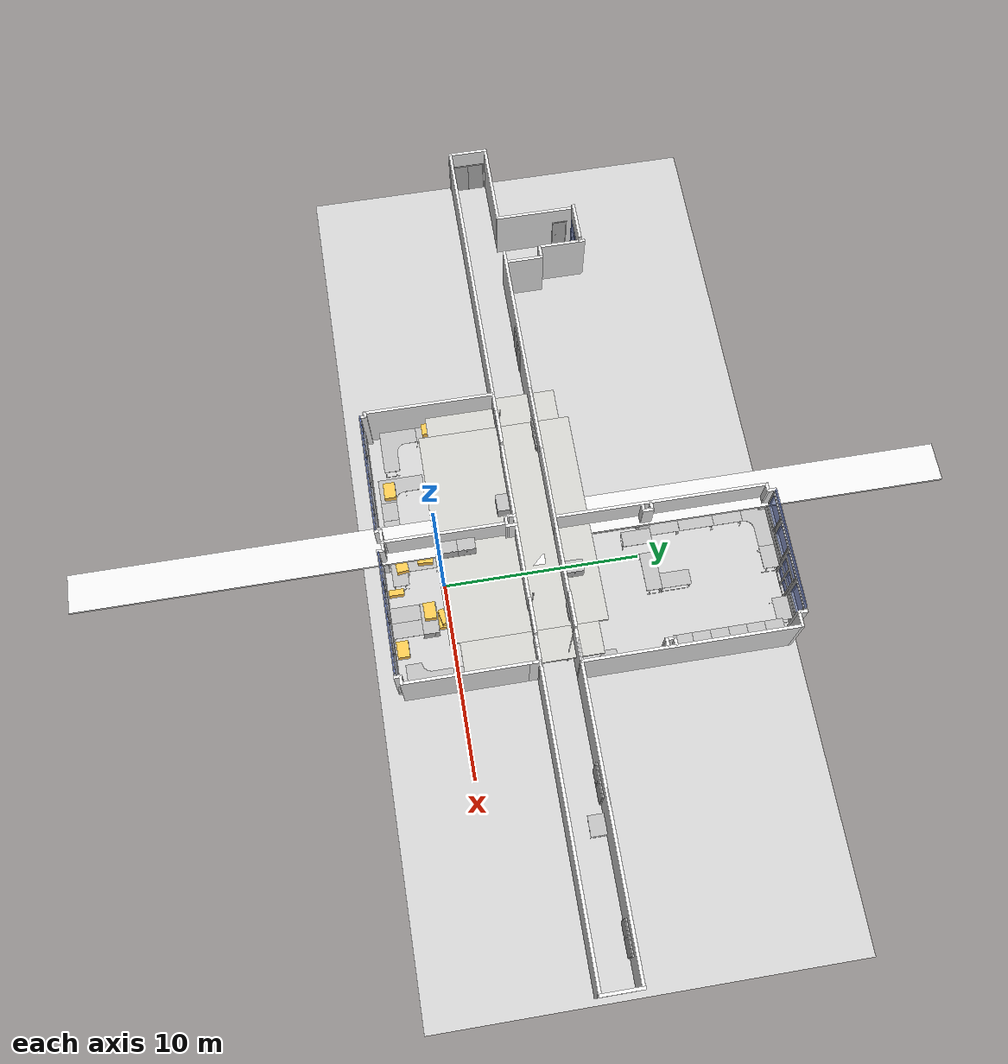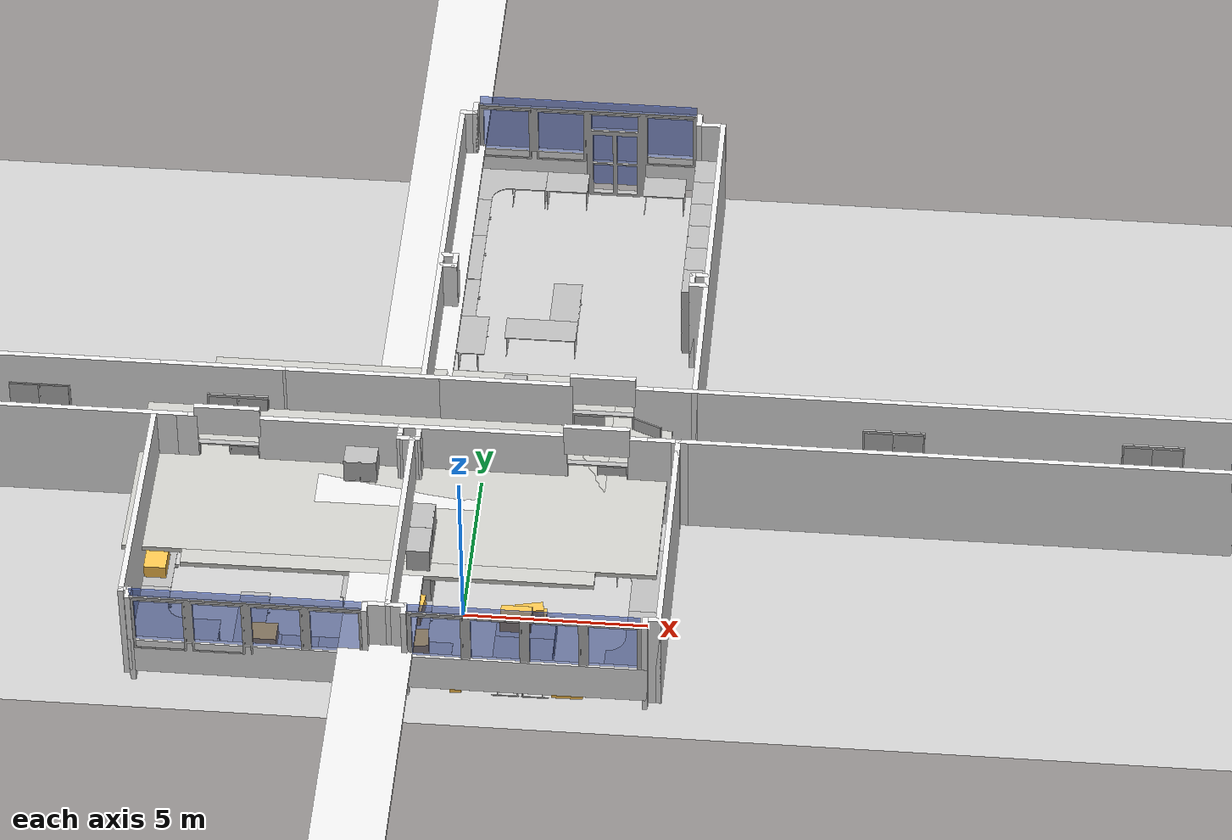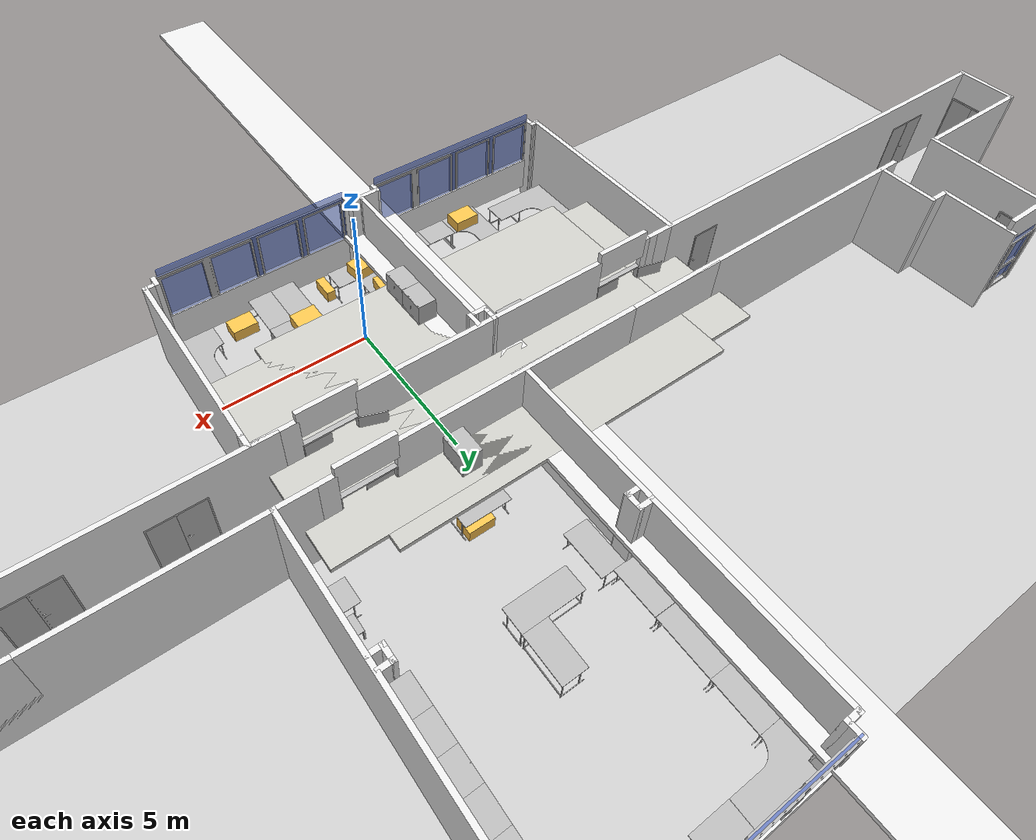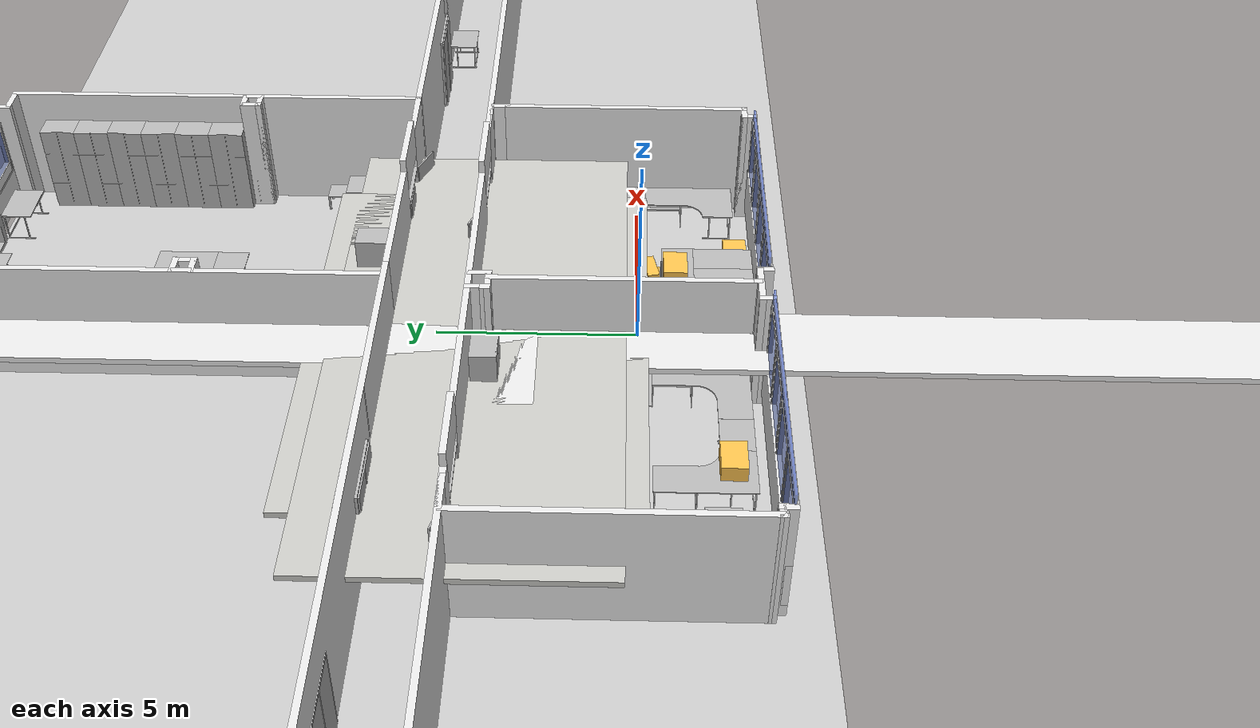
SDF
<sdf version="1.7">
 <world name="default">
  <scene><shadows>0</shadows><ambient>0.4 0.4 0.4 1</ambient><background>0.7 0.7 0.7 1</background></scene>
  <light name="sun1" type="directional">
   <cast_shadows>0</cast_shadows>
   <pose>0 0 5 0 -0 0</pose>
   <diffuse>0.5 0.5 0.5 1</diffuse>
   <specular>0.1 0.1 0.1 1</specular>
   <attenuation>
    <range>1000</range>
    <constant>0.9</constant>
    <linear>0.01</linear>
    <quadratic>0.001</quadratic>
   </attenuation>
   <direction>-0.5 0.5 -1</direction>
   <spot><inner_angle>0</inner_angle><outer_angle>0</outer_angle><falloff>0</falloff></spot>
  </light>
  <light name="sun2" type="directional">
   <cast_shadows>0</cast_shadows>
   <pose>0 0 5 0 -0 0</pose>
   <diffuse>0.5 0.5 0.5 1</diffuse>
   <specular>0.1 0.1 0.1 1</specular>
   <attenuation>
    <range>1000</range>
    <constant>0.9</constant>
    <linear>0.01</linear>
    <quadratic>0.001</quadratic>
   </attenuation>
   <direction>0.5 -0.5 -1</direction>
   <spot><inner_angle>0</inner_angle><outer_angle>0</outer_angle><falloff>0</falloff></spot>
  </light>
  <physics name="default_physics" default="0" type="ode">
   <max_step_size>0.001</max_step_size>
   <real_time_factor>1</real_time_factor>
   <real_time_update_rate>1000</real_time_update_rate>
  </physics>
  <scene><ambient>0.4 0.4 0.4 1</ambient><background>0.7 0.7 0.7 1</background><shadows>1</shadows></scene>
  <spherical_coordinates>
   <surface_model>EARTH_WGS84</surface_model>
   <latitude_deg>0</latitude_deg>
   <longitude_deg>0</longitude_deg>
   <elevation>0</elevation>
   <heading_deg>0</heading_deg>
  </spherical_coordinates>
  <model name="podlaha">
   <static>1</static>
   <link name="link">
    <collision name="collision">
     <geometry><plane><normal>0 0 1</normal><size>45 21</size></plane></geometry>
     <surface><friction><ode><mu>100</mu><mu2>50</mu2></ode></friction></surface>
    </collision>
    <visual name="visual">
     <cast_shadows>0</cast_shadows>
     <geometry><plane><normal>0 0 1</normal><size>45 21</size></plane></geometry>
     <material>
      <script>
       <uri>model://my_ground_plane/materials/scripts</uri>
       <uri>model://my_ground_plane/materials/textures/</uri>
       <name>MyGroundPlane/Image</name>
      </script>
     </material>
    </visual>
    <velocity_decay><linear>0</linear><angular>0</angular></velocity_decay>
   </link>
   <pose>-1.5 6.5 0 0 -0 0</pose>
  </model>
  <model name="skola">
   <pose>-1.5 7 0.34 0 -0 0</pose>
   <link name="Wall_0">
    <collision name="Wall_0_Collision">
     <geometry><box><size>4 0.15 3.18</size></box></geometry>
     <pose>0 0 1.25 0 -0 0</pose>
    </collision>
    <visual name="Wall_0_Visual">
     <pose>0 0 1.25 0 -0 0</pose>
     <geometry><box><size>4 0.15 3.18</size></box></geometry>
     <material>
      <script><uri>file://media/materials/scripts/gazebo.material</uri><name>Gazebo/White</name></script>
      <ambient>0.921569 0.807843 0.615686 1</ambient>
     </material>
     <meta><layer>0</layer></meta>
    </visual>
    <pose>-2.46639 -3.07195 0 0 -0 0</pose>
   </link>
   <link name="Wall_1">
    <collision name="Wall_1_Collision">
     <geometry><box><size>0.5 0.15 3.18</size></box></geometry>
     <pose>0 0 1.25 0 -0 0</pose>
    </collision>
    <visual name="Wall_1_Visual">
     <pose>0 0 1.25 0 -0 0</pose>
     <geometry><box><size>0.5 0.15 3.18</size></box></geometry>
     <material>
      <script><uri>file://media/materials/scripts/gazebo.material</uri><name>Gazebo/White</name></script>
      <ambient>0.921569 0.807843 0.615686 1</ambient>
     </material>
     <meta><layer>0</layer></meta>
    </visual>
    <pose>-0.541394 -3.24695 0 0 -0 -1.5708</pose>
   </link>
   <link name="Strop_1">
    <collision name="Strop_1_Collision">
     <geometry><box><size>6.9 14.5 0.15</size></box></geometry>
     <pose>0 0 1.25 0 -0 0</pose>
    </collision>
    <visual name="Strop_1_Visual">
     <pose>0 0 1.25 0 -0 0</pose>
     <geometry><box><size>6.9 14.5 0.15</size></box></geometry>
     <material>
      <script><uri>file://media/materials/scripts/gazebo.material</uri><name>Gazebo/CeilingTiled</name></script>
      <ambient>0.921569 0.807843 0.615686 1</ambient>
     </material>
     <meta><layer>0</layer></meta>
    </visual>
    <pose>-0.541394 -3.24695 0 0 -0 -1.5708</pose>
   </link>
   <link name="Strop_2">
    <collision name="Strop_2_Collision">
     <geometry><box><size>7.9 11.2 0.15</size></box></geometry>
     <pose>0 0 1.25 0 -0 0</pose>
    </collision>
    <visual name="Strop_2_Visual">
     <pose>0 0 1.25 0 -0 0</pose>
     <geometry><box><size>7.9 11.2 0.15</size></box></geometry>
     <material>
      <script><uri>file://media/materials/scripts/gazebo.material</uri><name>Gazebo/CeilingTiled</name></script>
      <ambient>0.921569 0.807843 0.615686 1</ambient>
     </material>
     <meta><layer>0</layer></meta>
    </visual>
    <pose>-0.541394 -3.24695 0 0 -0 -1.5708</pose>
   </link>
   <link name="Strop_3">
    <collision name="Strop_3_Collision">
     <geometry><box><size>44.5 2 0.15</size></box></geometry>
     <pose>0 0 1.25 0 -0 0</pose>
    </collision>
    <visual name="Strop_3_Visual">
     <pose>0 0 1.25 0 -0 0</pose>
     <geometry><box><size>44.5 2 0.15</size></box></geometry>
     <material>
      <script><uri>file://media/materials/scripts/gazebo.material</uri><name>Gazebo/White</name></script>
      <ambient>0.921569 0.807843 0.615686 1</ambient>
     </material>
     <meta><layer>0</layer></meta>
    </visual>
    <pose>-0.541394 -3.24695 0 0 -0 -1.5708</pose>
   </link>
   <link name="Strop_4">
    <collision name="Strop_4_Collision">
     <geometry><box><size>2.8 4.5 0.15</size></box></geometry>
     <pose>0 0 1.25 0 -0 0</pose>
    </collision>
    <visual name="Strop_4_Visual">
     <pose>0 0 1.25 0 -0 0</pose>
     <geometry><box><size>2.8 4.5 0.15</size></box></geometry>
     <material>
      <script><uri>file://media/materials/scripts/gazebo.material</uri><name>Gazebo/White</name></script>
      <ambient>0.921569 0.807843 0.615686 1</ambient>
     </material>
     <meta><layer>0</layer></meta>
    </visual>
    <pose>-0.541394 -3.24695 0 0 -0 -1.5708</pose>
   </link>
   <link name="Wall_100">
    <collision name="Wall_100_Collision">
     <geometry><box><size>0.6 0.15 3.18</size></box></geometry>
     <pose>0 0 1.25 0 -0 0</pose>
    </collision>
    <visual name="Wall_100_Visual">
     <pose>0 0 1.25 0 -0 0</pose>
     <geometry><box><size>0.6 0.15 3.18</size></box></geometry>
     <material>
      <script><uri>file://media/materials/scripts/gazebo.material</uri><name>Gazebo/White</name></script>
      <ambient>0.921569 0.807843 0.615686 1</ambient>
     </material>
     <meta><layer>0</layer></meta>
    </visual>
    <pose>6.98329 -3.07195 0 0 -0 0</pose>
   </link>
   <link name="Wall_102">
    <collision name="Wall_102_Collision">
     <geometry><box><size>2.13 0.15 3.18</size></box></geometry>
     <pose>0 0 1.25 0 -0 0</pose>
    </collision>
    <visual name="Wall_102_Visual">
     <pose>0 0 1.25 0 -0 0</pose>
     <geometry><box><size>2.13 0.15 3.18</size></box></geometry>
     <material>
      <script><uri>file://media/materials/scripts/gazebo.material</uri><name>Gazebo/White</name></script>
      <ambient>0.921569 0.807843 0.615686 1</ambient>
     </material>
     <meta><layer>0</layer></meta>
    </visual>
    <pose>-22.3067 -2.1155 0 0 -0 1.5708</pose>
   </link>
   <link name="Wall_104">
    <collision name="Wall_104_Collision">
     <geometry><box><size>3.44231 0.15 3.18</size></box></geometry>
     <pose>0 0 1.25 0 -0 0</pose>
    </collision>
    <visual name="Wall_104_Visual">
     <pose>0 0 1.25 0 -0 0</pose>
     <geometry><box><size>3.44231 0.15 3.18</size></box></geometry>
     <material>
      <script><uri>file://media/materials/scripts/gazebo.material</uri><name>Gazebo/White</name></script>
      <ambient>0.921569 0.807843 0.615686 1</ambient>
     </material>
     <meta><layer>0</layer></meta>
    </visual>
    <pose>-5.66059 -1.12687 0 0 -0 3.14076</pose>
   </link>
   <link name="Wall_12">
    <collision name="Wall_12_Collision">
     <geometry><box><size>0.25 0.15 3.18</size></box></geometry>
     <pose>0 0 1.25 0 -0 0</pose>
    </collision>
    <visual name="Wall_12_Visual">
     <pose>0 0 1.25 0 -0 0</pose>
     <geometry><box><size>0.25 0.15 3.18</size></box></geometry>
     <material>
      <script><uri>file://media/materials/scripts/gazebo.material</uri><name>Gazebo/White</name></script>
      <ambient>1 1 1 1</ambient>
     </material>
     <meta><layer>0</layer></meta>
    </visual>
    <pose>-0.191552 -9.67173 0 0 -0 -1.57396</pose>
   </link>
   <link name="Wall_13">
    <collision name="Wall_13_Collision">
     <geometry><box><size>0.75 0.15 3.18</size></box></geometry>
     <pose>0 0 1.25 0 -0 0</pose>
    </collision>
    <visual name="Wall_13_Visual">
     <pose>0 0 1.25 0 -0 0</pose>
     <geometry><box><size>0.75 0.15 3.18</size></box></geometry>
     <material>
      <script><uri>file://media/materials/scripts/gazebo.material</uri><name>Gazebo/White</name></script>
      <ambient>0.921569 0.807843 0.615686 1</ambient>
     </material>
     <meta><layer>0</layer></meta>
    </visual>
    <pose>-0.491552 -9.72173 0 0 -0 -3.14084</pose>
   </link>
   <link name="Wall_14">
    <collision name="Wall_14_Collision">
     <geometry><box><size>0.390555 0.15 3.18</size></box></geometry>
     <pose>0 0 1.25 0 -0 0</pose>
    </collision>
    <visual name="Wall_14_Visual">
     <pose>0 0 1.25 0 -0 0</pose>
     <geometry><box><size>0.390555 0.15 3.18</size></box></geometry>
     <material>
      <script><uri>file://media/materials/scripts/gazebo.material</uri><name>Gazebo/White</name></script>
      <ambient>0.921569 0.807843 0.615686 1</ambient>
     </material>
     <meta><layer>0</layer></meta>
    </visual>
    <pose>-0.791394 -9.84223 0 0 -0 -1.5708</pose>
   </link>
   <link name="Wall_15">
    <collision name="Wall_15_Collision">
     <geometry><box><size>6.47657 0.15 1.2</size></box></geometry>
     <pose>0 0 0.6 0 -0 0</pose>
    </collision>
    <visual name="Wall_15_Visual">
     <pose>0 0 0.6 0 -0 0</pose>
     <geometry><box><size>6.47657 0.15 1.2</size></box></geometry>
     <material>
      <script><uri>file://media/materials/scripts/gazebo.material</uri><name>Gazebo/White</name></script>
      <ambient>0.921569 0.807843 0.615686 1</ambient>
     </material>
     <meta><layer>0</layer></meta>
    </visual>
    <pose>-3.94685 -9.95469 0 0 -0 3.13912</pose>
   </link>
   <link name="Wall_16">
    <collision name="Wall_16_Collision">
     <geometry><box><size>6.2 0.05 2</size></box></geometry>
     <pose>0 0 0.6 0 -0 0</pose>
    </collision>
    <visual name="Wall_16_Visual">
     <pose>0 0 0.6 0 -0 0</pose>
     <geometry><box><size>6.2 0.05 2</size></box></geometry>
     <material>
      <script><uri>file://media/materials/scripts/gazebo.material</uri><name>Gazebo/BlueTransparent</name></script>
      <ambient>0.921569 0.807843 0.615686 1</ambient>
     </material>
     <meta><layer>0</layer></meta>
    </visual>
    <pose>-3.94685 -9.95469 1.5 0 -0 3.13912</pose>
   </link>
   <link name="Wall_17">
    <collision name="Wall_17_Collision">
     <geometry><box><size>6.2 0.05 2</size></box></geometry>
     <pose>0 0 0.6 0 -0 0</pose>
    </collision>
    <visual name="Wall_17_Visual">
     <pose>0 0 0.6 0 -0 0</pose>
     <geometry><box><size>6.2 0.05 2</size></box></geometry>
     <material>
      <script><uri>file://media/materials/scripts/gazebo.material</uri><name>Gazebo/BlueTransparent</name></script>
      <ambient>0.921569 0.807843 0.615686 1</ambient>
     </material>
     <meta><layer>0</layer></meta>
    </visual>
    <pose>3.44 -9.95469 1.5 0 -0 3.13912</pose>
   </link>
   <link name="Wall_18">
    <collision name="Wall_18_Collision">
     <geometry><box><size>1.15224 0.15 3.18</size></box></geometry>
     <pose>0 0 1.25 0 -0 0</pose>
    </collision>
    <visual name="Wall_18_Visual">
     <pose>0 0 1.25 0 -0 0</pose>
     <geometry><box><size>1.15224 0.15 3.18</size></box></geometry>
     <material>
      <script><uri>file://media/materials/scripts/gazebo.material</uri><name>Gazebo/White</name></script>
      <ambient>0.921569 0.807843 0.615686 1</ambient>
     </material>
     <meta><layer>0</layer></meta>
    </visual>
    <pose>-6.70571 -3.072 0 0 -0 3.1396</pose>
   </link>
   <link name="Wall_2">
    <collision name="Wall_2_Collision">
     <geometry><box><size>0.25 0.15 3.18</size></box></geometry>
     <pose>0 0 1.25 0 -0 0</pose>
    </collision>
    <visual name="Wall_2_Visual">
     <pose>0 0 1.25 0 -0 0</pose>
     <geometry><box><size>0.25 0.15 3.18</size></box></geometry>
     <material>
      <script><uri>file://media/materials/scripts/gazebo.material</uri><name>Gazebo/White</name></script>
      <ambient>1 1 1 1</ambient>
     </material>
     <meta><layer>0</layer></meta>
    </visual>
    <pose>-0.541394 -3.47195 0 0 -0 -1.5708</pose>
   </link>
   <link name="Wall_22">
    <collision name="Wall_22_Collision">
     <geometry><box><size>6.74777 0.15 3.18</size></box></geometry>
     <pose>0 0 1.25 0 -0 0</pose>
    </collision>
    <visual name="Wall_22_Visual">
     <pose>0 0 1.25 0 -0 0</pose>
     <geometry><box><size>6.74777 0.15 3.18</size></box></geometry>
     <material>
      <script><uri>file://media/materials/scripts/gazebo.material</uri><name>Gazebo/White</name></script>
      <ambient>0.921569 0.807843 0.615686 1</ambient>
     </material>
     <meta><layer>0</layer></meta>
    </visual>
    <pose>-7.30671 -6.4345 0 0 -0 -1.5708</pose>
   </link>
   <link name="Wall_23">
    <collision name="Wall_23_Collision">
     <geometry><box><size>0.15 0.15 3.18</size></box></geometry>
     <pose>0 0 1.25 0 -0 0</pose>
    </collision>
    <visual name="Wall_23_Visual">
     <pose>0 0 1.25 0 -0 0</pose>
     <geometry><box><size>0.15 0.15 3.18</size></box></geometry>
     <material>
      <script><uri>file://media/materials/scripts/gazebo.material</uri><name>Gazebo/White</name></script>
      <ambient>1 1 1 1</ambient>
     </material>
     <meta><layer>0</layer></meta>
    </visual>
    <pose>-7.30671 -9.7035 0 0 -0 0</pose>
   </link>
   <link name="Wall_25">
    <collision name="Wall_25_Collision">
     <geometry><box><size>0.15 0.15 3.18</size></box></geometry>
     <pose>0 0 1.25 0 -0 0</pose>
    </collision>
    <visual name="Wall_25_Visual">
     <pose>0 0 1.25 0 -0 0</pose>
     <geometry><box><size>0.15 0.15 3.18</size></box></geometry>
     <material>
      <script><uri>file://media/materials/scripts/gazebo.material</uri><name>Gazebo/White</name></script>
      <ambient>0.921569 0.807843 0.615686 1</ambient>
     </material>
     <meta><layer>0</layer></meta>
    </visual>
    <pose>-7.30671 -9.7035 0 0 -0 0</pose>
   </link>
   <link name="Wall_27">
    <collision name="Wall_27_Collision">
     <geometry><box><size>0.351876 0.15 3.18</size></box></geometry>
     <pose>0 0 1.25 0 -0 0</pose>
    </collision>
    <visual name="Wall_27_Visual">
     <pose>0 0 1.25 0 -0 0</pose>
     <geometry><box><size>0.351876 0.15 3.18</size></box></geometry>
     <material>
      <script><uri>file://media/materials/scripts/gazebo.material</uri><name>Gazebo/White</name></script>
      <ambient>0.921569 0.807843 0.615686 1</ambient>
     </material>
     <meta><layer>0</layer></meta>
    </visual>
    <pose>-7.20607 -9.69568 0 0 -0 0.077526</pose>
   </link>
   <link name="Wall_28">
    <collision name="Wall_28_Collision">
     <geometry><box><size>0.409049 0.15 3.18</size></box></geometry>
     <pose>0 0 1.25 0 -0 0</pose>
    </collision>
    <visual name="Wall_28_Visual">
     <pose>0 0 1.25 0 -0 0</pose>
     <geometry><box><size>0.409049 0.15 3.18</size></box></geometry>
     <material>
      <script><uri>file://media/materials/scripts/gazebo.material</uri><name>Gazebo/White</name></script>
      <ambient>0.921569 0.807843 0.615686 1</ambient>
     </material>
     <meta><layer>0</layer></meta>
    </visual>
    <pose>-7.09996 -9.81737 0 0 -0 -1.58888</pose>
   </link>
   <link name="Wall_3">
    <collision name="Wall_3_Collision">
     <geometry><box><size>0.5 0.15 3.18</size></box></geometry>
     <pose>0 0 1.25 0 -0 0</pose>
    </collision>
    <visual name="Wall_3_Visual">
     <pose>0 0 1.25 0 -0 0</pose>
     <geometry><box><size>0.5 0.15 3.18</size></box></geometry>
     <material>
      <script><uri>file://media/materials/scripts/gazebo.material</uri><name>Gazebo/White</name></script>
      <ambient>0.921569 0.807843 0.615686 1</ambient>
     </material>
     <meta><layer>0</layer></meta>
    </visual>
    <pose>-0.366552 -3.52173 0 0 -0 0.001291</pose>
   </link>
   <link name="Wall_31">
    <collision name="Wall_31_Collision">
     <geometry><box><size>0.3 0.15 3.18</size></box></geometry>
     <pose>0 0 1.25 0 -0 0</pose>
    </collision>
    <visual name="Wall_31_Visual">
     <pose>0 0 1.25 0 -0 0</pose>
     <geometry><box><size>0.3 0.15 3.18</size></box></geometry>
     <material>
      <script><uri>file://media/materials/scripts/gazebo.material</uri><name>Gazebo/White</name></script>
      <ambient>1 1 1 1</ambient>
     </material>
     <meta><layer>0</layer></meta>
    </visual>
    <pose>-0.116709 -3.5215 0 0 -0 0</pose>
   </link>
   <link name="Wall_34">
    <collision name="Wall_34_Collision">
     <geometry><box><size>4.6 0.15 3.18</size></box></geometry>
     <pose>0 0 1.25 0 -0 0</pose>
    </collision>
    <visual name="Wall_34_Visual">
     <pose>0 0 1.25 0 -0 0</pose>
     <geometry><box><size>4.6 0.15 3.18</size></box></geometry>
     <material>
      <script><uri>file://media/materials/scripts/gazebo.material</uri><name>Gazebo/White</name></script>
      <ambient>0.921569 0.807843 0.615686 1</ambient>
     </material>
     <meta><layer>0</layer></meta>
    </visual>
    <pose>1.68361 -3.07195 0 0 -0 0</pose>
   </link>
   <link name="Wall_41">
    <collision name="Wall_41_Collision">
     <geometry><box><size>0.592756 0.15 3.18</size></box></geometry>
     <pose>0 0 1.25 0 -0 0</pose>
    </collision>
    <visual name="Wall_41_Visual">
     <pose>0 0 1.25 0 -0 0</pose>
     <geometry><box><size>0.592756 0.15 3.18</size></box></geometry>
     <material>
      <script><uri>file://media/materials/scripts/gazebo.material</uri><name>Gazebo/White</name></script>
      <ambient>0.921569 0.807843 0.615686 1</ambient>
     </material>
     <meta><layer>0</layer></meta>
    </visual>
    <pose>-0.043425 -3.30013 0 0 -0 -1.56305</pose>
   </link>
   <link name="Wall_43">
    <collision name="Wall_43_Collision">
     <geometry><box><size>0.55 0.15 3.18</size></box></geometry>
     <pose>0 0 1.25 0 -0 0</pose>
    </collision>
    <visual name="Wall_43_Visual">
     <pose>0 0 1.25 0 -0 0</pose>
     <geometry><box><size>0.55 0.15 3.18</size></box></geometry>
     <material>
      <script><uri>file://media/materials/scripts/gazebo.material</uri><name>Gazebo/White</name></script>
      <ambient>0.921569 0.807843 0.615686 1</ambient>
     </material>
     <meta><layer>0</layer></meta>
    </visual>
    <pose>0.008291 -9.7215 0 0 -0 0</pose>
   </link>
   <link name="Wall_45">
    <collision name="Wall_45_Collision">
     <geometry><box><size>0.4 0.15 3.18</size></box></geometry>
     <pose>0 0 1.25 0 -0 0</pose>
    </collision>
    <visual name="Wall_45_Visual">
     <pose>0 0 1.25 0 -0 0</pose>
     <geometry><box><size>0.4 0.15 3.18</size></box></geometry>
     <material>
      <script><uri>file://media/materials/scripts/gazebo.material</uri><name>Gazebo/White</name></script>
      <ambient>0.921569 0.807843 0.615686 1</ambient>
     </material>
     <meta><layer>0</layer></meta>
    </visual>
    <pose>0.25291 -9.8465 0 0 -0 -1.5708</pose>
   </link>
   <link name="Wall_48">
    <collision name="Wall_48_Collision">
     <geometry><box><size>6.6 0.15 1.2</size></box></geometry>
     <pose>0 0 0.6 0 -0 0</pose>
    </collision>
    <visual name="Wall_48_Visual">
     <pose>0 0 0.6 0 -0 0</pose>
     <geometry><box><size>6.6 0.15 1.2</size></box></geometry>
     <material>
      <script><uri>file://media/materials/scripts/gazebo.material</uri><name>Gazebo/White</name></script>
      <ambient>0.921569 0.807843 0.615686 1</ambient>
     </material>
     <meta><layer>0</layer></meta>
    </visual>
    <pose>3.43329 -9.9715 0 0 -0 0</pose>
   </link>
   <link name="Wall_49">
    <collision name="Wall_49_Collision">
     <geometry><box><size>6.2 0.05 3.1</size></box></geometry>
     <pose>0 0 0.6 0 -0 0</pose>
    </collision>
    <visual name="Wall_49_Visual">
     <pose>0 0 0.6 0 -0 0</pose>
     <geometry><box><size>6.2 0.05 3.1</size></box></geometry>
     <material>
      <script><uri>file://media/materials/scripts/gazebo.material</uri><name>Gazebo/BlueTransparent</name></script>
      <ambient>0.921569 0.807843 0.615686 1</ambient>
     </material>
     <meta><layer>0</layer></meta>
    </visual>
    <pose>3.43329 9.95 1 0 -0 3.14</pose>
   </link>
   <link name="Wall_5">
    <collision name="Wall_5_Collision">
     <geometry><box><size>6.25 0.15 3.18</size></box></geometry>
     <pose>0 0 1.25 0 -0 0</pose>
    </collision>
    <visual name="Wall_5_Visual">
     <pose>0 0 1.25 0 -0 0</pose>
     <geometry><box><size>6.25 0.15 3.18</size></box></geometry>
     <material>
      <script><uri>file://media/materials/scripts/gazebo.material</uri><name>Gazebo/White</name></script>
      <ambient>0.921569 0.807843 0.615686 1</ambient>
     </material>
     <meta><layer>0</layer></meta>
    </visual>
    <pose>-0.191552 -6.57173 0 0 -0 -1.57075</pose>
   </link>
   <link name="Wall_50">
    <collision name="Wall_50_Collision">
     <geometry><box><size>0.4 0.15 3.18</size></box></geometry>
     <pose>0 0 1.25 0 -0 0</pose>
    </collision>
    <visual name="Wall_50_Visual">
     <pose>0 0 1.25 0 -0 0</pose>
     <geometry><box><size>0.4 0.15 3.18</size></box></geometry>
     <material>
      <script><uri>file://media/materials/scripts/gazebo.material</uri><name>Gazebo/White</name></script>
      <ambient>0.921569 0.807843 0.615686 1</ambient>
     </material>
     <meta><layer>0</layer></meta>
    </visual>
    <pose>6.65829 -9.8465 0 0 -0 1.5708</pose>
   </link>
   <link name="Wall_53">
    <collision name="Wall_53_Collision">
     <geometry><box><size>0.5 0.15 3.18</size></box></geometry>
     <pose>0 0 1.25 0 -0 0</pose>
    </collision>
    <visual name="Wall_53_Visual">
     <pose>0 0 1.25 0 -0 0</pose>
     <geometry><box><size>0.5 0.15 3.18</size></box></geometry>
     <material>
      <script><uri>file://media/materials/scripts/gazebo.material</uri><name>Gazebo/White</name></script>
      <ambient>0.921569 0.807843 0.615686 1</ambient>
     </material>
     <meta><layer>0</layer></meta>
    </visual>
    <pose>6.83329 -9.7215 0 0 -0 0</pose>
   </link>
   <link name="Wall_59">
    <collision name="Wall_59_Collision">
     <geometry><box><size>6.35 0.15 3.18</size></box></geometry>
     <pose>0 0 1.25 0 -0 0</pose>
    </collision>
    <visual name="Wall_59_Visual">
     <pose>0 0 1.25 0 -0 0</pose>
     <geometry><box><size>6.35 0.15 3.18</size></box></geometry>
     <material>
      <script><uri>file://media/materials/scripts/gazebo.material</uri><name>Gazebo/White</name></script>
      <ambient>0.921569 0.807843 0.615686 1</ambient>
     </material>
     <meta><layer>0</layer></meta>
    </visual>
    <pose>7.00829 -6.6215 0 0 -0 1.5708</pose>
   </link>
   <link name="Wall_65">
    <collision name="Wall_65_Collision">
     <geometry><box><size>0.58 0.15 3.18</size></box></geometry>
     <pose>0 0 1.25 0 -0 0</pose>
    </collision>
    <visual name="Wall_65_Visual">
     <pose>0 0 1.25 0 -0 0</pose>
     <geometry><box><size>0.58 0.15 3.18</size></box></geometry>
     <material>
      <script><uri>file://media/materials/scripts/gazebo.material</uri><name>Gazebo/White</name></script>
      <ambient>0.921569 0.807843 0.615686 1</ambient>
     </material>
     <meta><layer>0</layer></meta>
    </visual>
    <pose>7.00829 -3.3065 0 0 -0 1.5708</pose>
   </link>
   <link name="Wall_67">
    <collision name="Wall_67_Collision">
     <geometry><box><size>1.2 0.15 3.18</size></box></geometry>
     <pose>0 0 1.25 0 -0 0</pose>
    </collision>
    <visual name="Wall_67_Visual">
     <pose>0 0 1.25 0 -0 0</pose>
     <geometry><box><size>1.2 0.15 3.18</size></box></geometry>
     <material>
      <script><uri>file://media/materials/scripts/gazebo.material</uri><name>Gazebo/White</name></script>
      <ambient>0.921569 0.807843 0.615686 1</ambient>
     </material>
     <meta><layer>0</layer></meta>
    </visual>
    <pose>6.23329 -3.07195 0 0 -0 3.14159</pose>
   </link>
   <link name="Wall_69">
    <collision name="Wall_69_Collision">
     <geometry><box><size>8 0.15 3.18</size></box></geometry>
     <pose>0 0 1.25 0 -0 0</pose>
    </collision>
    <visual name="Wall_69_Visual">
     <pose>0 0 1.25 0 -0 0</pose>
     <geometry><box><size>8 0.15 3.18</size></box></geometry>
     <material>
      <script><uri>file://media/materials/scripts/gazebo.material</uri><name>Gazebo/White</name></script>
      <ambient>0.921569 0.807843 0.615686 1</ambient>
     </material>
     <meta><layer>0</layer></meta>
    </visual>
    <pose>-0.03 -1.12824 0 0 -0 3.14159</pose>
   </link>
   <link name="Wall_73">
    <collision name="Wall_73_Collision">
     <geometry><box><size>1.75 0.15 3.18</size></box></geometry>
     <pose>0 0 1.25 0 -0 0</pose>
    </collision>
    <visual name="Wall_73_Visual">
     <pose>0 0 1.25 0 -0 0</pose>
     <geometry><box><size>1.75 0.15 3.18</size></box></geometry>
     <material>
      <script><uri>file://media/materials/scripts/gazebo.material</uri><name>Gazebo/White</name></script>
      <ambient>0.921569 0.807843 0.615686 1</ambient>
     </material>
     <meta><layer>0</layer></meta>
    </visual>
    <pose>6.51211 -1.12837 0 0 -0 -0.000159</pose>
   </link>
   <link name="Wall_75">
    <collision name="Wall_75_Collision">
     <geometry><box><size>10.9 0.15 3.18</size></box></geometry>
     <pose>0 0 1.25 0 -0 0</pose>
    </collision>
    <visual name="Wall_75_Visual">
     <pose>0 0 1.25 0 -0 0</pose>
     <geometry><box><size>10.9 0.15 3.18</size></box></geometry>
     <material>
      <script><uri>file://media/materials/scripts/gazebo.material</uri><name>Gazebo/White</name></script>
      <ambient>0.921569 0.807843 0.615686 1</ambient>
     </material>
     <meta><layer>0</layer></meta>
    </visual>
    <pose>7.31229 4.2465 0 0 -0 1.5708</pose>
   </link>
   <link name="Wall_77">
    <collision name="Wall_77_Collision">
     <geometry><box><size>0.75 0.15 3.18</size></box></geometry>
     <pose>0 0 1.25 0 -0 0</pose>
    </collision>
    <visual name="Wall_77_Visual">
     <pose>0 0 1.25 0 -0 0</pose>
     <geometry><box><size>0.75 0.15 3.18</size></box></geometry>
     <material>
      <script><uri>file://media/materials/scripts/gazebo.material</uri><name>Gazebo/White</name></script>
      <ambient>0.921569 0.807843 0.615686 1</ambient>
     </material>
     <meta><layer>0</layer></meta>
    </visual>
    <pose>7.01229 9.6215 0 0 -0 3.14159</pose>
   </link>
   <link name="Wall_79">
    <collision name="Wall_79_Collision">
     <geometry><box><size>0.5 0.15 3.18</size></box></geometry>
     <pose>0 0 1.25 0 -0 0</pose>
    </collision>
    <visual name="Wall_79_Visual">
     <pose>0 0 1.25 0 -0 0</pose>
     <geometry><box><size>0.5 0.15 3.18</size></box></geometry>
     <material>
      <script><uri>file://media/materials/scripts/gazebo.material</uri><name>Gazebo/White</name></script>
      <ambient>0.921569 0.807843 0.615686 1</ambient>
     </material>
     <meta><layer>0</layer></meta>
    </visual>
    <pose>6.63 9.7965 0 0 -0 1.5708</pose>
   </link>
   <link name="Wall_80">
    <collision name="Wall_80_Collision">
     <geometry><box><size>3.1 0.15 1.2</size></box></geometry>
     <pose>0 0 0.6 0 -0 0</pose>
    </collision>
    <visual name="Wall_80_Visual">
     <pose>0 0 0.6 0 -0 0</pose>
     <geometry><box><size>3.1 0.15 1.2</size></box></geometry>
     <material>
      <script><uri>file://media/materials/scripts/gazebo.material</uri><name>Gazebo/White</name></script>
      <ambient>0.921569 0.807843 0.615686 1</ambient>
     </material>
     <meta><layer>0</layer></meta>
    </visual>
    <pose>1.82 9.9715 0 0 -0 3.14159</pose>
   </link>
   <link name="Wall_81">
    <collision name="Wall_81_Collision">
     <geometry><box><size>1.7 0.15 1.2</size></box></geometry>
     <pose>0 0 0.6 0 -0 0</pose>
    </collision>
    <visual name="Wall_81_Visual">
     <pose>0 0 0.6 0 -0 0</pose>
     <geometry><box><size>1.7 0.15 1.2</size></box></geometry>
     <material>
      <script><uri>file://media/materials/scripts/gazebo.material</uri><name>Gazebo/White</name></script>
      <ambient>0.921569 0.807843 0.615686 1</ambient>
     </material>
     <meta><layer>0</layer></meta>
    </visual>
    <pose>5.92 9.9715 0 0 -0 3.14159</pose>
   </link>
   <link name="Wall_82">
    <collision name="Wall_82_Collision">
     <geometry><box><size>0.5 0.15 3.18</size></box></geometry>
     <pose>0 0 1.25 0 -0 0</pose>
    </collision>
    <visual name="Wall_82_Visual">
     <pose>0 0 1.25 0 -0 0</pose>
     <geometry><box><size>0.5 0.15 3.18</size></box></geometry>
     <material>
      <script><uri>file://media/materials/scripts/gazebo.material</uri><name>Gazebo/White</name></script>
      <ambient>0.921569 0.807843 0.615686 1</ambient>
     </material>
     <meta><layer>0</layer></meta>
    </visual>
    <pose>0.212291 9.7965 0 0 -0 -1.5708</pose>
   </link>
   <link name="Wall_87">
    <collision name="Wall_87_Collision">
     <geometry><box><size>0.5 0.15 3.18</size></box></geometry>
     <pose>0 0 1.25 0 -0 0</pose>
    </collision>
    <visual name="Wall_87_Visual">
     <pose>0 0 1.25 0 -0 0</pose>
     <geometry><box><size>0.5 0.15 3.18</size></box></geometry>
     <material>
      <script><uri>file://media/materials/scripts/gazebo.material</uri><name>Gazebo/White</name></script>
      <ambient>0.921569 0.807843 0.615686 1</ambient>
     </material>
     <meta><layer>0</layer></meta>
    </visual>
    <pose>0.037291 9.6215 0 0 -0 3.14159</pose>
   </link>
   <link name="Wall_88">
    <collision name="Wall_88_Collision">
     <geometry><box><size>10.75 0.15 3.18</size></box></geometry>
     <pose>0 0 1.25 0 -0 0</pose>
    </collision>
    <visual name="Wall_88_Visual">
     <pose>0 0 1.25 0 -0 0</pose>
     <geometry><box><size>10.75 0.15 3.18</size></box></geometry>
     <material>
      <script><uri>file://media/materials/scripts/gazebo.material</uri><name>Gazebo/White</name></script>
      <ambient>0.921569 0.807843 0.615686 1</ambient>
     </material>
     <meta><layer>0</layer></meta>
    </visual>
    <pose>-0.137709 4.3215 0 0 -0 -1.5708</pose>
   </link>
   <link name="Wall_90">
    <collision name="Wall_90_Collision">
     <geometry><box><size>0.55 0.15 3.18</size></box></geometry>
     <pose>0 0 1.25 0 -0 0</pose>
    </collision>
    <visual name="Wall_90_Visual">
     <pose>0 0 1.25 0 -0 0</pose>
     <geometry><box><size>0.55 0.15 3.18</size></box></geometry>
     <material>
      <script><uri>file://media/materials/scripts/gazebo.material</uri><name>Gazebo/White</name></script>
      <ambient>0.921569 0.807843 0.615686 1</ambient>
     </material>
     <meta><layer>0</layer></meta>
    </visual>
    <pose>7.11229 3.0625 0 0 -0 3.14159</pose>
   </link>
   <link name="Wall_92">
    <collision name="Wall_92_Collision">
     <geometry><box><size>0.55 0.15 3.18</size></box></geometry>
     <pose>0 0 1.25 0 -0 0</pose>
    </collision>
    <visual name="Wall_92_Visual">
     <pose>0 0 1.25 0 -0 0</pose>
     <geometry><box><size>0.55 0.15 3.18</size></box></geometry>
     <material>
      <script><uri>file://media/materials/scripts/gazebo.material</uri><name>Gazebo/White</name></script>
      <ambient>0.921569 0.807843 0.615686 1</ambient>
     </material>
     <meta><layer>0</layer></meta>
    </visual>
    <pose>6.91229 3.2625 0 0 -0 1.5708</pose>
   </link>
   <link name="Wall_94">
    <collision name="Wall_94_Collision">
     <geometry><box><size>0.5 0.15 3.18</size></box></geometry>
     <pose>0 0 1.25 0 -0 0</pose>
    </collision>
    <visual name="Wall_94_Visual">
     <pose>0 0 1.25 0 -0 0</pose>
     <geometry><box><size>0.5 0.15 3.18</size></box></geometry>
     <material>
      <script><uri>file://media/materials/scripts/gazebo.material</uri><name>Gazebo/White</name></script>
      <ambient>0.921569 0.807843 0.615686 1</ambient>
     </material>
     <meta><layer>0</layer></meta>
    </visual>
    <pose>7.08729 3.4625 0 0 -0 0</pose>
   </link>
   <link name="Wall_98">
    <collision name="Wall_98_Collision">
     <geometry><box><size>2.1 0.15 1.01</size></box></geometry>
     <pose>0 0 1.25 0 -0 0</pose>
    </collision>
    <visual name="Wall_98_Visual">
     <pose>0 0 1.25 0 -0 0</pose>
     <geometry><box><size>2.1 0.15 1.01</size></box></geometry>
     <material>
      <script><uri>file://media/materials/scripts/gazebo.material</uri><name>Gazebo/White</name></script>
      <ambient>0.921569 0.807843 0.615686 1</ambient>
     </material>
     <meta><layer>0</layer></meta>
    </visual>
    <pose>22.1 -2.1085 1.425 0 -0 -1.5708</pose>
   </link>
   <link name="Wall_119">
    <collision name="Wall_119_Collision">
     <geometry><box><size>2 0.07 2.1</size></box></geometry>
     <pose>0 0 1.25 0 -0 0</pose>
    </collision>
    <visual name="Wall_119_Visual">
     <pose>0 0 1.25 0 -0 0</pose>
     <geometry><box><size>2 0.07 2.1</size></box></geometry>
     <material>
      <script><uri>file://media/materials/scripts/gazebo.material</uri><name>Gazebo/BlueTransparent</name></script>
      <ambient>0.921569 0.807843 0.615686 1</ambient>
     </material>
     <meta><layer>0</layer></meta>
    </visual>
    <pose>22.1 -2.1085 -0.2 0 -0 -1.5708</pose>
   </link>
   <link name="Wall_99">
    <collision name="Wall_99_Collision">
     <geometry><box><size>0.55 0.15 3.18</size></box></geometry>
     <pose>0 0 1.25 0 -0 0</pose>
    </collision>
    <visual name="Wall_99_Visual">
     <pose>0 0 1.25 0 -0 0</pose>
     <geometry><box><size>0.55 0.15 3.18</size></box></geometry>
     <material>
      <script><uri>file://media/materials/scripts/gazebo.material</uri><name>Gazebo/White</name></script>
      <ambient>0.921569 0.807843 0.615686 1</ambient>
     </material>
     <meta><layer>0</layer></meta>
    </visual>
    <pose>0.265 3.525 0 0 -0 1.5708</pose>
   </link>
   <link name="Wall_97">
    <collision name="Wall_97_Collision">
     <geometry><box><size>0.55 0.15 3.18</size></box></geometry>
     <pose>0 0 1.25 0 -0 0</pose>
    </collision>
    <visual name="Wall_97_Visual">
     <pose>0 0 1.25 0 -0 0</pose>
     <geometry><box><size>0.55 0.15 3.18</size></box></geometry>
     <material>
      <script><uri>file://media/materials/scripts/gazebo.material</uri><name>Gazebo/White</name></script>
      <ambient>0.921569 0.807843 0.615686 1</ambient>
     </material>
     <meta><layer>0</layer></meta>
    </visual>
    <pose>0.064 3.3 0 0 -0 3.14159</pose>
   </link>
   <link name="Wall_96">
    <collision name="Wall_96_Collision">
     <geometry><box><size>0.55 0.15 3.18</size></box></geometry>
     <pose>0 0 1.25 0 -0 0</pose>
    </collision>
    <visual name="Wall_96_Visual">
     <pose>0 0 1.25 0 -0 0</pose>
     <geometry><box><size>0.55 0.15 3.18</size></box></geometry>
     <material>
      <script><uri>file://media/materials/scripts/gazebo.material</uri><name>Gazebo/White</name></script>
      <ambient>0.921569 0.807843 0.615686 1</ambient>
     </material>
     <meta><layer>0</layer></meta>
    </visual>
    <pose>0.064 3.725 0 0 -0 3.14159</pose>
   </link>
   <link name="Wall_107">
    <collision name="Wall_107_Collision">
     <geometry><box><size>16 0.15 3.18</size></box></geometry>
     <pose>0 0 1.25 0 -0 0</pose>
    </collision>
    <visual name="Wall_107_Visual">
     <pose>0 0 1.25 0 -0 0</pose>
     <geometry><box><size>16 0.15 3.18</size></box></geometry>
     <material>
      <script><uri>file://media/materials/scripts/gazebo.material</uri><name>Gazebo/White</name></script>
      <ambient>0.921569 0.807843 0.615686 1</ambient>
     </material>
     <meta><layer>0</layer></meta>
    </visual>
    <pose>-7.7 -1.12824 0 0 -0 3.14159</pose>
   </link>
   <link name="Wall_103">
    <collision name="Wall_103_Collision">
     <geometry><box><size>16 0.15 3.18</size></box></geometry>
     <pose>0 0 1.25 0 -0 0</pose>
    </collision>
    <visual name="Wall_103_Visual">
     <pose>0 0 1.25 0 -0 0</pose>
     <geometry><box><size>16 0.15 3.18</size></box></geometry>
     <material>
      <script><uri>file://media/materials/scripts/gazebo.material</uri><name>Gazebo/White</name></script>
      <ambient>0.921569 0.807843 0.615686 1</ambient>
     </material>
     <meta><layer>0</layer></meta>
    </visual>
    <pose>-14.38 -3.072 0 0 -0 3.14159</pose>
   </link>
   <link name="Wall_106">
    <collision name="Wall_106_Collision">
     <geometry><box><size>16 0.15 3.18</size></box></geometry>
     <pose>0 0 1.25 0 -0 0</pose>
    </collision>
    <visual name="Wall_106_Visual">
     <pose>0 0 1.25 0 -0 0</pose>
     <geometry><box><size>16 0.15 3.18</size></box></geometry>
     <material>
      <script><uri>file://media/materials/scripts/gazebo.material</uri><name>Gazebo/White</name></script>
      <ambient>0.921569 0.807843 0.615686 1</ambient>
     </material>
     <meta><layer>0</layer></meta>
    </visual>
    <pose>14.17 -3.07195 0 0 -0 3.14159</pose>
   </link>
   <link name="Wall_108">
    <collision name="Wall_108_Collision">
     <geometry><box><size>16 0.15 3.18</size></box></geometry>
     <pose>0 0 1.25 0 -0 0</pose>
    </collision>
    <visual name="Wall_108_Visual">
     <pose>0 0 1.25 0 -0 0</pose>
     <geometry><box><size>16 0.15 3.18</size></box></geometry>
     <material>
      <script><uri>file://media/materials/scripts/gazebo.material</uri><name>Gazebo/White</name></script>
      <ambient>0.921569 0.807843 0.615686 1</ambient>
     </material>
     <meta><layer>0</layer></meta>
    </visual>
    <pose>14.17 -1.12824 0 0 -0 3.14159</pose>
   </link>
   <link name="Wall_109">
    <collision name="Wall_109_Collision">
     <geometry><box><size>4.5 0.15 3.18</size></box></geometry>
     <pose>0 0 1.25 0 -0 0</pose>
    </collision>
    <visual name="Wall_109_Visual">
     <pose>0 0 1.25 0 -0 0</pose>
     <geometry><box><size>4.5 0.15 3.18</size></box></geometry>
     <material>
      <script><uri>file://media/materials/scripts/gazebo.material</uri><name>Gazebo/White</name></script>
      <ambient>0.921569 0.807843 0.615686 1</ambient>
     </material>
     <meta><layer>0</layer></meta>
    </visual>
    <pose>-20.1 -1.12824 0 0 -0 3.14159</pose>
   </link>
   <link name="Wall_110">
    <collision name="Wall_110_Collision">
     <geometry><box><size>4.3 0.15 3.18</size></box></geometry>
     <pose>0 0 1.25 0 -0 0</pose>
    </collision>
    <visual name="Wall_110_Visual">
     <pose>0 0 1.25 0 -0 0</pose>
     <geometry><box><size>4.3 0.15 3.18</size></box></geometry>
     <material>
      <script><uri>file://media/materials/scripts/gazebo.material</uri><name>Gazebo/White</name></script>
      <ambient>0.921569 0.807843 0.615686 1</ambient>
     </material>
     <meta><layer>0</layer></meta>
    </visual>
    <pose>-17.8 0.94176 0 0 -0 1.57</pose>
   </link>
   <link name="Wall_111">
    <collision name="Wall_111_Collision">
     <geometry><box><size>2 0.15 3.18</size></box></geometry>
     <pose>0 0 1.25 0 -0 0</pose>
    </collision>
    <visual name="Wall_111_Visual">
     <pose>0 0 1.25 0 -0 0</pose>
     <geometry><box><size>2 0.15 3.18</size></box></geometry>
     <material>
      <script><uri>file://media/materials/scripts/gazebo.material</uri><name>Gazebo/White</name></script>
      <ambient>0.921569 0.807843 0.615686 1</ambient>
     </material>
     <meta><layer>0</layer></meta>
    </visual>
    <pose>-15 -0.12824 0 0 -0 1.57</pose>
   </link>
   <link name="Wall_112">
    <collision name="Wall_112_Collision">
     <geometry><box><size>2.55 0.15 3.18</size></box></geometry>
     <pose>0 0 1.25 0 -0 0</pose>
    </collision>
    <visual name="Wall_112_Visual">
     <pose>0 0 1.25 0 -0 0</pose>
     <geometry><box><size>2.55 0.15 3.18</size></box></geometry>
     <material>
      <script><uri>file://media/materials/scripts/gazebo.material</uri><name>Gazebo/White</name></script>
      <ambient>0.921569 0.807843 0.615686 1</ambient>
     </material>
     <meta><layer>0</layer></meta>
    </visual>
    <pose>-15.65 2 0 0 -0 1.57</pose>
   </link>
   <link name="Wall_113">
    <collision name="Wall_113_Collision">
     <geometry><box><size>0.65 0.15 3.18</size></box></geometry>
     <pose>0 0 1.25 0 -0 0</pose>
    </collision>
    <visual name="Wall_113_Visual">
     <pose>0 0 1.25 0 -0 0</pose>
     <geometry><box><size>0.65 0.15 3.18</size></box></geometry>
     <material>
      <script><uri>file://media/materials/scripts/gazebo.material</uri><name>Gazebo/White</name></script>
      <ambient>0.921569 0.807843 0.615686 1</ambient>
     </material>
     <meta><layer>0</layer></meta>
    </visual>
    <pose>-15.4 0.795 0 0 -0 3.14159</pose>
   </link>
   <link name="Wall_114">
    <collision name="Wall_114_Collision">
     <geometry><box><size>1.65 0.15 3.18</size></box></geometry>
     <pose>0 0 1.25 0 -0 0</pose>
    </collision>
    <visual name="Wall_114_Visual">
     <pose>0 0 1.25 0 -0 0</pose>
     <geometry><box><size>1.65 0.15 3.18</size></box></geometry>
     <material>
      <script><uri>file://media/materials/scripts/gazebo.material</uri><name>Gazebo/White</name></script>
      <ambient>0.921569 0.807843 0.615686 1</ambient>
     </material>
     <meta><layer>0</layer></meta>
    </visual>
    <pose>14.17 -1.12824 0 0 -0 3.14159</pose>
   </link>
   <link name="Wall_115">
    <collision name="Wall_115_Collision">
     <geometry><box><size>1.8 0.15 1.01</size></box></geometry>
     <pose>0 0 1.25 0 -0 0</pose>
    </collision>
    <visual name="Wall_115_Visual">
     <pose>0 0 1.25 0 -0 0</pose>
     <geometry><box><size>1.8 0.15 1.01</size></box></geometry>
     <material>
      <script><uri>file://media/materials/scripts/gazebo.material</uri><name>Gazebo/White</name></script>
      <ambient>0.921569 0.807843 0.615686 1</ambient>
     </material>
     <meta><layer>0</layer></meta>
    </visual>
    <pose>-5.3 -3.072 1.425 0 -0 3.14159</pose>
   </link>
   <link name="Wall_116">
    <collision name="Wall_116_Collision">
     <geometry><box><size>1.8 0.15 1.01</size></box></geometry>
     <pose>0 0 1.25 0 -0 0</pose>
    </collision>
    <visual name="Wall_116_Visual">
     <pose>0 0 1.25 0 -0 0</pose>
     <geometry><box><size>1.8 0.15 1.01</size></box></geometry>
     <material>
      <script><uri>file://media/materials/scripts/gazebo.material</uri><name>Gazebo/White</name></script>
      <ambient>0.921569 0.807843 0.615686 1</ambient>
     </material>
     <meta><layer>0</layer></meta>
    </visual>
    <pose>4.8 -3.072 1.425 0 -0 3.14159</pose>
   </link>
   <link name="Wall_117">
    <collision name="Wall_117_Collision">
     <geometry><box><size>1.8 0.15 1.01</size></box></geometry>
     <pose>0 0 1.25 0 -0 0</pose>
    </collision>
    <visual name="Wall_117_Visual">
     <pose>0 0 1.25 0 -0 0</pose>
     <geometry><box><size>1.8 0.15 1.01</size></box></geometry>
     <material>
      <script><uri>file://media/materials/scripts/gazebo.material</uri><name>Gazebo/White</name></script>
      <ambient>0.921569 0.807843 0.615686 1</ambient>
     </material>
     <meta><layer>0</layer></meta>
    </visual>
    <pose>4.8 -1.12824 1.425 0 -0 3.14159</pose>
   </link>
   <link name="Wall_118">
    <collision name="Wall_118_Collision">
     <geometry><box><size>2.1 0.15 1.03</size></box></geometry>
     <pose>0 0 1.25 0 -0 0</pose>
    </collision>
    <visual name="Wall_118_Visual">
     <pose>0 0 1.25 0 -0 0</pose>
     <geometry><box><size>2.1 0.15 1.03</size></box></geometry>
     <material>
      <script><uri>file://media/materials/scripts/gazebo.material</uri><name>Gazebo/White</name></script>
      <ambient>0.921569 0.807843 0.615686 1</ambient>
     </material>
     <meta><layer>0</layer></meta>
    </visual>
    <pose>-16.7 3 1.42 0 -0 3.14159</pose>
   </link>
   <link name="Wall_120">
    <collision name="Wall_120_Collision">
     <geometry><box><size>2 0.07 2.1</size></box></geometry>
     <pose>0 0 1.25 0 -0 0</pose>
    </collision>
    <visual name="Wall_120_Visual">
     <pose>0 0 1.25 0 -0 0</pose>
     <geometry><box><size>2 0.07 2.1</size></box></geometry>
     <material>
      <script><uri>file://media/materials/scripts/gazebo.material</uri><name>Gazebo/BlueTransparent</name></script>
      <ambient>0.921569 0.807843 0.615686 1</ambient>
     </material>
     <meta><layer>0</layer></meta>
    </visual>
    <pose>-16.7 3 -0.2 0 -0 3.14159</pose>
   </link>
   <static>1</static>
  </model>
  <model name="stul_150_SE_1_112_1">
   <pose>-1.2 -1 0 0 -0 1.57</pose>
   <static>1</static>
   <link name="stul_150_collision">
    <collision name="stul_150_collision">
     <geometry><mesh><uri>model://stul_150/meshes/model.dae</uri></mesh></geometry>
    </collision>
    <visual name="stul_150_mesh">
     <cast_shadows>0</cast_shadows>
     <geometry><mesh><uri>model://stul_150/meshes/model.dae</uri></mesh></geometry>
     <material>
      <script>
       <uri>model://stul_150/material/scripts</uri>
       <uri>model://stul_150/material/textures</uri>
       <name>stul_150/Diffuse</name>
      </script>
     </material>
    </visual>
   </link>
  </model>
  <model name="2_stul_150_SE_1_112">
   <pose>-0.85 -2.15 0 0 -0 3.14</pose>
   <static>1</static>
   <link name="stul_150_collision">
    <collision name="stul_150_collision">
     <geometry><mesh><uri>model://stul_150/meshes/model.dae</uri></mesh></geometry>
    </collision>
    <visual name="stul_150_mesh">
     <cast_shadows>0</cast_shadows>
     <geometry><mesh><uri>model://stul_150/meshes/model.dae</uri></mesh></geometry>
     <material>
      <script>
       <uri>model://stul_150/material/scripts</uri>
       <uri>model://stul_150/material/textures</uri>
       <name>stul_150/Diffuse</name>
      </script>
     </material>
    </visual>
   </link>
  </model>
  <model name="stul_150_SE_1_112_3">
   <pose>1.4 -2.15 0 0 0 -1.57</pose>
   <static>1</static>
   <link name="stul_150_collision">
    <collision name="stul_150_collision">
     <geometry><mesh><uri>model://stul_150/meshes/model.dae</uri></mesh></geometry>
    </collision>
    <visual name="stul_150_mesh">
     <cast_shadows>0</cast_shadows>
     <geometry><mesh><uri>model://stul_150/meshes/model.dae</uri></mesh></geometry>
     <material>
      <script>
       <uri>model://stul_150/material/scripts</uri>
       <uri>model://stul_150/material/textures</uri>
       <name>stul_150/Diffuse</name>
      </script>
     </material>
    </visual>
   </link>
  </model>
  <model name="stul_150_SE_1_112_4">
   <pose>2.2 -2.15 0 0 -0 1.57</pose>
   <static>1</static>
   <link name="stul_150_collision">
    <collision name="stul_150_collision">
     <geometry><mesh><uri>model://stul_150/meshes/model.dae</uri></mesh></geometry>
    </collision>
    <visual name="stul_150_mesh">
     <cast_shadows>0</cast_shadows>
     <geometry><mesh><uri>model://stul_150/meshes/model.dae</uri></mesh></geometry>
     <material>
      <script>
       <uri>model://stul_150/material/scripts</uri>
       <uri>model://stul_150/material/textures</uri>
       <name>stul_150/Diffuse</name>
      </script>
     </material>
    </visual>
   </link>
  </model>
  <model name="stul_180_SE_1_112_1">
   <pose>2 2.9 0 0 -0 1.57</pose>
   <static>1</static>
   <link name="stul_180_collision">
    <collision name="stul_180_collision">
     <geometry><mesh><uri>model://stul_180/meshes/model.dae</uri></mesh></geometry>
    </collision>
    <visual name="stul_180_mesh">
     <cast_shadows>0</cast_shadows>
     <geometry><mesh><uri>model://stul_180/meshes/model.dae</uri></mesh></geometry>
     <material>
      <script>
       <uri>model://stul_180/material/scripts</uri>
       <uri>model://stul_180/material/textures</uri>
       <name>stul_180/Diffuse</name>
      </script>
     </material>
    </visual>
   </link>
  </model>
  <model name="stul_160_SE_1_112_1">
   <pose>1.8 -1 0 0 -0 0</pose>
   <static>1</static>
   <link name="stul_160_collision">
    <collision name="stul_160_collision">
     <geometry><mesh><uri>model://stul_160/meshes/model.dae</uri></mesh></geometry>
    </collision>
    <visual name="stul_160_mesh">
     <cast_shadows>0</cast_shadows>
     <geometry><mesh><uri>model://stul_160/meshes/model.dae</uri></mesh></geometry>
     <material>
      <script>
       <uri>model://stul_160/material/scripts</uri>
       <uri>model://stul_160/material/textures</uri>
       <name>stul_160/Diffuse</name>
      </script>
     </material>
    </visual>
   </link>
  </model>
  <model name="stul_l_pravy_1_112_1">
   <pose>4 -0.2 0 0 0 -1.57</pose>
   <static>1</static>
   <link name="stul_l_pravy_collision">
    <collision name="stul_l_pravy_collision">
     <geometry><mesh><uri>model://stul_l_pravy/meshes/model.dae</uri></mesh></geometry>
    </collision>
    <visual name="stul_l_pravy_mesh">
     <cast_shadows>0</cast_shadows>
     <geometry><mesh><uri>model://stul_l_pravy/meshes/model.dae</uri></mesh></geometry>
     <material>
      <script>
       <uri>model://stul_l_pravy/material/scripts</uri>
       <uri>model://stul_l_pravy/material/textures</uri>
       <name>stul_l_pravy/Diffuse</name>
      </script>
     </material>
    </visual>
   </link>
  </model>
  <model name="stul_l_pravy_1_112_2">
   <pose>0.3 3.8 0 0 0 -1.57</pose>
   <static>1</static>
   <link name="stul_l_pravy_collision">
    <collision name="stul_l_pravy_collision">
     <geometry><mesh><uri>model://stul_l_pravy/meshes/model.dae</uri></mesh></geometry>
    </collision>
    <visual name="stul_l_pravy_mesh">
     <cast_shadows>0</cast_shadows>
     <geometry><mesh><uri>model://stul_l_pravy/meshes/model.dae</uri></mesh></geometry>
     <material>
      <script>
       <uri>model://stul_l_pravy/material/scripts</uri>
       <uri>model://stul_l_pravy/material/textures</uri>
       <name>stul_l_pravy/Diffuse</name>
      </script>
     </material>
    </visual>
   </link>
  </model>
  <model name="stul_l_levy_1_112_1">
   <pose>4.65 0.95 0 0 -0 1.57</pose>
   <static>1</static>
   <link name="stul_l_levy_collision">
    <collision name="stul_l_levy_collision">
     <geometry><mesh><uri>model://stul_l_levy/meshes/model.dae</uri></mesh></geometry>
    </collision>
    <visual name="stul_l_levy_mesh">
     <cast_shadows>0</cast_shadows>
     <geometry><mesh><uri>model://stul_l_levy/meshes/model.dae</uri></mesh></geometry>
     <material>
      <script>
       <uri>model://stul_l_levy/material/scripts</uri>
       <uri>model://stul_l_levy/material/textures</uri>
       <name>stul_l_levy/Diffuse</name>
      </script>
     </material>
    </visual>
   </link>
  </model>
  <model name="skrin_90_1_112_1">
   <pose>-1.2 1.35 0 0 -0 1.57</pose>
   <static>1</static>
   <link name="skrin_90_collision">
    <collision name="skrin_90_collision">
     <geometry><mesh><uri>model://skrin_90/meshes/model.dae</uri></mesh></geometry>
    </collision>
    <visual name="skrin_90">
     <cast_shadows>0</cast_shadows>
     <geometry><mesh><uri>model://skrin_90/meshes/model.dae</uri></mesh></geometry>
     <material>
      <script>
       <uri>model://skrin_90/material/scripts</uri>
       <uri>model://skrin_90/material/textures</uri>
       <name>skrin_90/Diffuse</name>
      </script>
     </material>
    </visual>
   </link>
  </model>
  <model name="skrin_90_1_112_2">
   <pose>-1.2 0.448 0 0 -0 1.57</pose>
   <static>1</static>
   <link name="skrin_90_collision">
    <collision name="skrin_90_collision">
     <geometry><mesh><uri>model://skrin_90/meshes/model.dae</uri></mesh></geometry>
    </collision>
    <visual name="skrin_90">
     <cast_shadows>0</cast_shadows>
     <geometry><mesh><uri>model://skrin_90/meshes/model.dae</uri></mesh></geometry>
     <material>
      <script>
       <uri>model://skrin_90/material/scripts</uri>
       <uri>model://skrin_90/material/textures</uri>
       <name>skrin_90/Diffuse</name>
      </script>
     </material>
    </visual>
   </link>
  </model>
  <model name="futra_112_1">
   <pose>3.305 3.93 0 0 -0 0</pose>
   <static>1</static>
   <link name="futra_160_collision">
    <collision name="futra_160_collision">
     <geometry><mesh><uri>model://futra_160/meshes/model.dae</uri></mesh></geometry>
    </collision>
    <visual name="futra_160">
     <cast_shadows>0</cast_shadows>
     <geometry><mesh><uri>model://futra_160/meshes/model.dae</uri></mesh></geometry>
     <material>
      <script>
       <uri>model://futra_160/material/scripts</uri>
       <uri>model://futra_160/material/textures</uri>
       <name>futra_160/Diffuse</name>
      </script>
     </material>
    </visual>
   </link>
  </model>
  <model name="dvere_sklikou_112_1">
   <pose>2.10865 4.12539 0 0 -0 2.8</pose>
   <static>1</static>
   <link name="dvere_80_sklikou_collision">
    <collision name="dvere_80_sklikou_collision">
     <geometry><mesh><uri>model://dvere_80_sklikou/meshes/model.dae</uri></mesh></geometry>
    </collision>
    <visual name="dvere_80_sklikou">
     <cast_shadows>0</cast_shadows>
     <geometry><mesh><uri>model://dvere_80_sklikou/meshes/model.dae</uri></mesh></geometry>
     <material>
      <script>
       <uri>model://dvere_80_sklikou/material/scripts</uri>
       <uri>model://dvere_80_sklikou/material/textures</uri>
       <name>dvere_80_sklikou/Diffuse</name>
      </script>
     </material>
    </visual>
   </link>
  </model>
  <model name="dvere_bezkliky_112_1">
   <pose>3.72 3.99 0 0 -0 0</pose>
   <static>1</static>
   <link name="dvere_80_bezkliky_collision">
    <collision name="dvere_80_bezkliky_collision">
     <geometry><mesh><uri>model://dvere_80_bezkliky/meshes/model.dae</uri></mesh></geometry>
    </collision>
    <visual name="dvere_80_bezkliky">
     <cast_shadows>0</cast_shadows>
     <geometry><mesh><uri>model://dvere_80_bezkliky/meshes/model.dae</uri></mesh></geometry>
     <material>
      <script>
       <uri>model://dvere_80_bezkliky/material/scripts</uri>
       <uri>model://dvere_80_bezkliky/material/textures</uri>
       <name>dvere_80_bezkliky/Diffuse</name>
      </script>
     </material>
    </visual>
   </link>
  </model>
  <model name="okna_mistnost1">
   <pose>-1.16 -3.01 1.18 0 -0 0</pose>
   <static>1</static>
   <link name="okna_collision">
    <collision name="okna_collision">
     <geometry><mesh><uri>model://okna/meshes/model.dae</uri></mesh></geometry>
    </collision>
    <visual name="okna_mesh">
     <cast_shadows>0</cast_shadows>
     <geometry><mesh><uri>model://okna/meshes/model.dae</uri></mesh></geometry>
     <material>
      <script>
       <uri>model://okna/material/scripts</uri>
       <uri>model://okna/material/textures</uri>
       <name>okna/Diffuse</name>
      </script>
     </material>
    </visual>
   </link>
  </model>
  <model name="futra_mistnost2">
   <pose>3.305 5.86 0 0 -0 0</pose>
   <static>1</static>
   <link name="futra_160_collision">
    <collision name="futra_160_collision">
     <geometry><mesh><uri>model://futra_160/meshes/model.dae</uri></mesh></geometry>
    </collision>
    <visual name="futra_160">
     <cast_shadows>0</cast_shadows>
     <geometry><mesh><uri>model://futra_160/meshes/model.dae</uri></mesh></geometry>
     <material>
      <script>
       <uri>model://futra_160/material/scripts</uri>
       <uri>model://futra_160/material/textures</uri>
       <name>futra_160/Diffuse</name>
      </script>
     </material>
    </visual>
   </link>
  </model>
  <model name="dvere_sklikou_mistnost2">
   <pose>4.53301 5.62047 0 0 0 -0.396925</pose>
   <static>1</static>
   <link name="dvere_80_sklikou_collision">
    <collision name="dvere_80_sklikou_collision">
     <geometry><mesh><uri>model://dvere_80_sklikou/meshes/model.dae</uri></mesh></geometry>
    </collision>
    <visual name="dvere_80_sklikou">
     <cast_shadows>0</cast_shadows>
     <geometry><mesh><uri>model://dvere_80_sklikou/meshes/model.dae</uri></mesh></geometry>
     <material>
      <script>
       <uri>model://dvere_80_sklikou/material/scripts</uri>
       <uri>model://dvere_80_sklikou/material/textures</uri>
       <name>dvere_80_sklikou/Diffuse</name>
      </script>
     </material>
    </visual>
   </link>
  </model>
  <model name="dvere_bezkliky_mistnost2">
   <pose>2.92 5.78 0 0 -0 3.14</pose>
   <static>1</static>
   <link name="dvere_80_bezkliky_collision">
    <collision name="dvere_80_bezkliky_collision">
     <geometry><mesh><uri>model://dvere_80_bezkliky/meshes/model.dae</uri></mesh></geometry>
    </collision>
    <visual name="dvere_80_bezkliky">
     <cast_shadows>0</cast_shadows>
     <geometry><mesh><uri>model://dvere_80_bezkliky/meshes/model.dae</uri></mesh></geometry>
     <material>
      <script>
       <uri>model://dvere_80_bezkliky/material/scripts</uri>
       <uri>model://dvere_80_bezkliky/material/textures</uri>
       <name>dvere_80_bezkliky/Diffuse</name>
      </script>
     </material>
    </visual>
   </link>
  </model>
  <model name="stul_80_SE_1_102_1">
   <pose>5.25 7.5 0 0 0 -1.57</pose>
   <static>1</static>
   <link name="stul_80_collision">
    <collision name="stul_80_collision">
     <geometry><mesh><uri>model://stul_80/meshes/model.dae</uri></mesh></geometry>
    </collision>
    <visual name="stul_80_mesh">
     <cast_shadows>0</cast_shadows>
     <geometry><mesh><uri>model://stul_80/meshes/model.dae</uri></mesh></geometry>
     <material>
      <script>
       <uri>model://stul_80/material/scripts</uri>
       <uri>model://stul_80/material/textures</uri>
       <name>stul_80/Diffuse</name>
      </script>
     </material>
    </visual>
   </link>
  </model>
  <model name="stul_120_mistnost2_1">
   <pose>1.35181 16.4961 0 0 -0 0</pose>
   <static>1</static>
   <link name="stul_120_collision">
    <collision name="stul_120_collision">
     <geometry><mesh><uri>model://stul_120/meshes/model.dae</uri></mesh></geometry>
    </collision>
    <visual name="stul_120_mesh">
     <cast_shadows>0</cast_shadows>
     <geometry><mesh><uri>model://stul_120/meshes/model.dae</uri></mesh></geometry>
     <material>
      <script>
       <uri>model://stul_120/material/scripts</uri>
       <uri>model://stul_120/material/textures</uri>
       <name>stul_120/Diffuse</name>
      </script>
     </material>
    </visual>
   </link>
  </model>
  <model name="stul_120_mistnost2_2">
   <pose>4.15 16.5 0 0 -0 0</pose>
   <static>1</static>
   <link name="stul_120_collision">
    <collision name="stul_120_collision">
     <geometry><mesh><uri>model://stul_120/meshes/model.dae</uri></mesh></geometry>
    </collision>
    <visual name="stul_120_mesh">
     <cast_shadows>0</cast_shadows>
     <geometry><mesh><uri>model://stul_120/meshes/model.dae</uri></mesh></geometry>
     <material>
      <script>
       <uri>model://stul_120/material/scripts</uri>
       <uri>model://stul_120/material/textures</uri>
       <name>stul_120/Diffuse</name>
      </script>
     </material>
    </visual>
   </link>
  </model>
  <model name="stul_l_levy_mistnost2">
   <pose>-0.4 16.25 0 0 -0 3.14</pose>
   <static>1</static>
   <link name="stul_l_levy_collision">
    <collision name="stul_l_levy_collision">
     <geometry><mesh><uri>model://stul_l_levy/meshes/model.dae</uri></mesh></geometry>
    </collision>
    <visual name="stul_l_levy_mesh">
     <cast_shadows>0</cast_shadows>
     <geometry><mesh><uri>model://stul_l_levy/meshes/model.dae</uri></mesh></geometry>
     <material>
      <script>
       <uri>model://stul_l_levy/material/scripts</uri>
       <uri>model://stul_l_levy/material/textures</uri>
       <name>stul_l_levy/Diffuse</name>
      </script>
     </material>
    </visual>
   </link>
  </model>
  <model name="stul_150_mistnost2_1">
   <pose>-1.15 14.85 0 0 -0 1.57</pose>
   <static>1</static>
   <link name="stul_150_collision">
    <collision name="stul_150_collision">
     <geometry><mesh><uri>model://stul_150/meshes/model.dae</uri></mesh></geometry>
    </collision>
    <visual name="stul_150_mesh">
     <cast_shadows>0</cast_shadows>
     <geometry><mesh><uri>model://stul_150/meshes/model.dae</uri></mesh></geometry>
     <material>
      <script>
       <uri>model://stul_150/material/scripts</uri>
       <uri>model://stul_150/material/textures</uri>
       <name>stul_150/Diffuse</name>
      </script>
     </material>
    </visual>
   </link>
  </model>
  <model name="stul_180_mistnost2_1">
   <pose>-1.15 13.2 0 0 -0 1.57</pose>
   <static>1</static>
   <link name="stul_180_collision">
    <collision name="stul_180_collision">
     <geometry><mesh><uri>model://stul_180/meshes/model.dae</uri></mesh></geometry>
    </collision>
    <visual name="stul_180_mesh">
     <cast_shadows>0</cast_shadows>
     <geometry><mesh><uri>model://stul_180/meshes/model.dae</uri></mesh></geometry>
     <material>
      <script>
       <uri>model://stul_180/material/scripts</uri>
       <uri>model://stul_180/material/textures</uri>
       <name>stul_180/Diffuse</name>
      </script>
     </material>
    </visual>
   </link>
  </model>
  <model name="stul_150_mistnost2_2">
   <pose>-1.14461 11.5378 0 0 -0 1.57</pose>
   <static>1</static>
   <link name="stul_150_collision">
    <collision name="stul_150_collision">
     <geometry><mesh><uri>model://stul_150/meshes/model.dae</uri></mesh></geometry>
    </collision>
    <visual name="stul_150_mesh">
     <cast_shadows>0</cast_shadows>
     <geometry><mesh><uri>model://stul_150/meshes/model.dae</uri></mesh></geometry>
     <material>
      <script>
       <uri>model://stul_150/material/scripts</uri>
       <uri>model://stul_150/material/textures</uri>
       <name>stul_150/Diffuse</name>
      </script>
     </material>
    </visual>
   </link>
  </model>
  <model name="stul_150_mistnost2_3">
   <pose>-0.75 10.05 0 0 -0 1.57</pose>
   <static>1</static>
   <link name="stul_150_collision">
    <collision name="stul_150_collision">
     <geometry><mesh><uri>model://stul_150/meshes/model.dae</uri></mesh></geometry>
    </collision>
    <visual name="stul_150_mesh">
     <cast_shadows>0</cast_shadows>
     <geometry><mesh><uri>model://stul_150/meshes/model.dae</uri></mesh></geometry>
     <material>
      <script>
       <uri>model://stul_150/material/scripts</uri>
       <uri>model://stul_150/material/textures</uri>
       <name>stul_150/Diffuse</name>
      </script>
     </material>
    </visual>
   </link>
  </model>
  <model name="stul_150_mistnost2_4">
   <pose>1.75 11.55 0 0 0 -1.57</pose>
   <static>1</static>
   <link name="stul_150_collision">
    <collision name="stul_150_collision">
     <geometry><mesh><uri>model://stul_150/meshes/model.dae</uri></mesh></geometry>
    </collision>
    <visual name="stul_150_mesh">
     <cast_shadows>0</cast_shadows>
     <geometry><mesh><uri>model://stul_150/meshes/model.dae</uri></mesh></geometry>
     <material>
      <script>
       <uri>model://stul_150/material/scripts</uri>
       <uri>model://stul_150/material/textures</uri>
       <name>stul_150/Diffuse</name>
      </script>
     </material>
    </visual>
   </link>
  </model>
  <model name="stul_200_mistnost2_1">
   <pose>1.15 10.4 0 0 -0 0</pose>
   <static>1</static>
   <link name="stul_200_collision">
    <collision name="stul_200_collision">
     <geometry><mesh><uri>model://stul_200/meshes/model.dae</uri></mesh></geometry>
    </collision>
    <visual name="stul_200_mesh">
     <cast_shadows>0</cast_shadows>
     <geometry><mesh><uri>model://stul_200/meshes/model.dae</uri></mesh></geometry>
     <material>
      <script>
       <uri>model://stul_200/material/scripts</uri>
       <uri>model://stul_200/material/textures</uri>
       <name>stul_200/Diffuse</name>
      </script>
     </material>
    </visual>
   </link>
  </model>
  <model name="skrin_90_mistnost2_1">
   <pose>5.4 11 0 0 0 -1.57</pose>
   <static>1</static>
   <link name="skrin_90_collision">
    <collision name="skrin_90_collision">
     <geometry><mesh><uri>model://skrin_90/meshes/model.dae</uri></mesh></geometry>
    </collision>
    <visual name="skrin_90">
     <cast_shadows>0</cast_shadows>
     <geometry><mesh><uri>model://skrin_90/meshes/model.dae</uri></mesh></geometry>
     <material>
      <script>
       <uri>model://skrin_90/material/scripts</uri>
       <uri>model://skrin_90/material/textures</uri>
       <name>skrin_90/Diffuse</name>
      </script>
     </material>
    </visual>
   </link>
  </model>
  <model name="skrin_90_mistnost2_2">
   <pose>5.4 11.9 0 0 0 -1.57</pose>
   <static>1</static>
   <link name="skrin_90_collision">
    <collision name="skrin_90_collision">
     <geometry><mesh><uri>model://skrin_90/meshes/model.dae</uri></mesh></geometry>
    </collision>
    <visual name="skrin_90">
     <cast_shadows>0</cast_shadows>
     <geometry><mesh><uri>model://skrin_90/meshes/model.dae</uri></mesh></geometry>
     <material>
      <script>
       <uri>model://skrin_90/material/scripts</uri>
       <uri>model://skrin_90/material/textures</uri>
       <name>skrin_90/Diffuse</name>
      </script>
     </material>
    </visual>
   </link>
  </model>
  <model name="skrin_90_mistnost2_3">
   <pose>5.4 12.8 0 0 0 -1.57</pose>
   <static>1</static>
   <link name="skrin_90_collision">
    <collision name="skrin_90_collision">
     <geometry><mesh><uri>model://skrin_90/meshes/model.dae</uri></mesh></geometry>
    </collision>
    <visual name="skrin_90">
     <cast_shadows>0</cast_shadows>
     <geometry><mesh><uri>model://skrin_90/meshes/model.dae</uri></mesh></geometry>
     <material>
      <script>
       <uri>model://skrin_90/material/scripts</uri>
       <uri>model://skrin_90/material/textures</uri>
       <name>skrin_90/Diffuse</name>
      </script>
     </material>
    </visual>
   </link>
  </model>
  <model name="skrin_90_mistnost2_4">
   <pose>5.4 13.7 0 0 0 -1.57</pose>
   <static>1</static>
   <link name="skrin_90_collision">
    <collision name="skrin_90_collision">
     <geometry><mesh><uri>model://skrin_90/meshes/model.dae</uri></mesh></geometry>
    </collision>
    <visual name="skrin_90">
     <cast_shadows>0</cast_shadows>
     <geometry><mesh><uri>model://skrin_90/meshes/model.dae</uri></mesh></geometry>
     <material>
      <script>
       <uri>model://skrin_90/material/scripts</uri>
       <uri>model://skrin_90/material/textures</uri>
       <name>skrin_90/Diffuse</name>
      </script>
     </material>
    </visual>
   </link>
  </model>
  <model name="skrin_90_mistnost2_5">
   <pose>5.4 14.6 0 0 0 -1.57</pose>
   <static>1</static>
   <link name="skrin_90_collision">
    <collision name="skrin_90_collision">
     <geometry><mesh><uri>model://skrin_90/meshes/model.dae</uri></mesh></geometry>
    </collision>
    <visual name="skrin_90">
     <cast_shadows>0</cast_shadows>
     <geometry><mesh><uri>model://skrin_90/meshes/model.dae</uri></mesh></geometry>
     <material>
      <script>
       <uri>model://skrin_90/material/scripts</uri>
       <uri>model://skrin_90/material/textures</uri>
       <name>skrin_90/Diffuse</name>
      </script>
     </material>
    </visual>
   </link>
  </model>
  <model name="skrin_90_mistnost2_6">
   <pose>5.4 15.5 0 0 0 -1.57</pose>
   <static>1</static>
   <link name="skrin_90_collision">
    <collision name="skrin_90_collision">
     <geometry><mesh><uri>model://skrin_90/meshes/model.dae</uri></mesh></geometry>
    </collision>
    <visual name="skrin_90">
     <cast_shadows>0</cast_shadows>
     <geometry><mesh><uri>model://skrin_90/meshes/model.dae</uri></mesh></geometry>
     <material>
      <script>
       <uri>model://skrin_90/material/scripts</uri>
       <uri>model://skrin_90/material/textures</uri>
       <name>skrin_90/Diffuse</name>
      </script>
     </material>
    </visual>
   </link>
  </model>
  <model name="skrin_90_mistnost2_7">
   <pose>0.8 6.448 0 0 -0 1.57</pose>
   <static>1</static>
   <link name="skrin_90_collision">
    <collision name="skrin_90_collision">
     <geometry><mesh><uri>model://skrin_90/meshes/model.dae</uri></mesh></geometry>
    </collision>
    <visual name="skrin_90">
     <cast_shadows>0</cast_shadows>
     <geometry><mesh><uri>model://skrin_90/meshes/model.dae</uri></mesh></geometry>
     <material>
      <script>
       <uri>model://skrin_90/material/scripts</uri>
       <uri>model://skrin_90/material/textures</uri>
       <name>skrin_90/Diffuse</name>
      </script>
     </material>
    </visual>
   </link>
  </model>
  <model name="stolecek_maly_mistnost2_1">
   <pose>5.65 7.9 0 0 -0 1.57</pose>
   <static>1</static>
   <link name="stolecek_maly_collision">
    <collision name="stolecek_maly_collision">
     <geometry><mesh><uri>model://stolecek_maly/meshes/model.dae</uri></mesh></geometry>
    </collision>
    <visual name="stolecek_maly_mesh">
     <cast_shadows>0</cast_shadows>
     <geometry><mesh><uri>model://stolecek_maly/meshes/model.dae</uri></mesh></geometry>
     <material>
      <script>
       <uri>model://stolecek_maly/material/scripts</uri>
       <uri>model://stolecek_maly/material/textures</uri>
       <name>stolecek_maly/Diffuse</name>
      </script>
     </material>
    </visual>
   </link>
  </model>
  <model name="okna_s_dvermi_mistnost2">
   <pose>-1.2 16.95 -0.025 0 -0 0</pose>
   <static>1</static>
   <link name="okna_s_dvermi_collision">
    <collision name="okna_s_dvermi_collision">
     <geometry><mesh><uri>model://okna_s_dvermi/meshes/model.dae</uri></mesh></geometry>
    </collision>
    <visual name="okna_s_dvermi_mesh">
     <cast_shadows>0</cast_shadows>
     <geometry><mesh><uri>model://okna_s_dvermi/meshes/model.dae</uri></mesh></geometry>
     <material>
      <script>
       <uri>model://okna_s_dvermi/material/scripts</uri>
       <uri>model://okna_s_dvermi/material/textures</uri>
       <name>okna_s_dvermi/Diffuse</name>
      </script>
     </material>
    </visual>
   </link>
  </model>
  <model name="futra_mistnost3">
   <pose>-6.795 3.93 0 0 -0 0</pose>
   <static>1</static>
   <link name="futra_160_collision">
    <collision name="futra_160_collision">
     <geometry><mesh><uri>model://futra_160/meshes/model.dae</uri></mesh></geometry>
    </collision>
    <visual name="futra_160">
     <cast_shadows>0</cast_shadows>
     <geometry><mesh><uri>model://futra_160/meshes/model.dae</uri></mesh></geometry>
     <material>
      <script>
       <uri>model://futra_160/material/scripts</uri>
       <uri>model://futra_160/material/textures</uri>
       <name>futra_160/Diffuse</name>
      </script>
     </material>
    </visual>
   </link>
  </model>
  <model name="dvere_sklikou_mistnost3">
   <pose>-8.00018 4.11255 0 0 -0 2.8828</pose>
   <static>1</static>
   <link name="dvere_80_sklikou_collision">
    <collision name="dvere_80_sklikou_collision">
     <geometry><mesh><uri>model://dvere_80_sklikou/meshes/model.dae</uri></mesh></geometry>
    </collision>
    <visual name="dvere_80_sklikou">
     <cast_shadows>0</cast_shadows>
     <geometry><mesh><uri>model://dvere_80_sklikou/meshes/model.dae</uri></mesh></geometry>
     <material>
      <script>
       <uri>model://dvere_80_sklikou/material/scripts</uri>
       <uri>model://dvere_80_sklikou/material/textures</uri>
       <name>dvere_80_sklikou/Diffuse</name>
      </script>
     </material>
    </visual>
   </link>
  </model>
  <model name="dvere_bezkliky_mistnost3">
   <pose>-6.38 3.99 0 0 -0 0</pose>
   <static>1</static>
   <link name="dvere_80_bezkliky_collision">
    <collision name="dvere_80_bezkliky_collision">
     <geometry><mesh><uri>model://dvere_80_bezkliky/meshes/model.dae</uri></mesh></geometry>
    </collision>
    <visual name="dvere_80_bezkliky">
     <cast_shadows>0</cast_shadows>
     <geometry><mesh><uri>model://dvere_80_bezkliky/meshes/model.dae</uri></mesh></geometry>
     <material>
      <script>
       <uri>model://dvere_80_bezkliky/material/scripts</uri>
       <uri>model://dvere_80_bezkliky/material/textures</uri>
       <name>dvere_80_bezkliky/Diffuse</name>
      </script>
     </material>
    </visual>
   </link>
  </model>
  <model name="skrin_90_low_mistnost3_1">
   <pose>-8.4 3.15 0 0 -0 1.57</pose>
   <static>1</static>
   <link name="skrin_90_low_collision">
    <collision name="skrin_90_low_collision">
     <geometry><mesh><uri>model://skrin_90_low/meshes/model.dae</uri></mesh></geometry>
    </collision>
    <visual name="skrin_90_low">
     <cast_shadows>0</cast_shadows>
     <geometry><mesh><uri>model://skrin_90_low/meshes/model.dae</uri></mesh></geometry>
     <material>
      <script>
       <uri>model://skrin_90_low/material/scripts</uri>
       <uri>model://skrin_90_low/material/textures</uri>
       <name>skrin_90_low/Diffuse</name>
      </script>
     </material>
    </visual>
   </link>
  </model>
  <model name="stul_150_mistnost3_1">
   <pose>-8.31 1.95 0 0 -0 1.57</pose>
   <static>1</static>
   <link name="stul_150_collision">
    <collision name="stul_150_collision">
     <geometry><mesh><uri>model://stul_150/meshes/model.dae</uri></mesh></geometry>
    </collision>
    <visual name="stul_150_mesh">
     <cast_shadows>0</cast_shadows>
     <geometry><mesh><uri>model://stul_150/meshes/model.dae</uri></mesh></geometry>
     <material>
      <script>
       <uri>model://stul_150/material/scripts</uri>
       <uri>model://stul_150/material/textures</uri>
       <name>stul_150/Diffuse</name>
      </script>
     </material>
    </visual>
   </link>
  </model>
  <model name="stul_150_mistnost3_2">
   <pose>-8.31 0.45 0 0 -0 1.57</pose>
   <static>1</static>
   <link name="stul_150_collision">
    <collision name="stul_150_collision">
     <geometry><mesh><uri>model://stul_150/meshes/model.dae</uri></mesh></geometry>
    </collision>
    <visual name="stul_150_mesh">
     <cast_shadows>0</cast_shadows>
     <geometry><mesh><uri>model://stul_150/meshes/model.dae</uri></mesh></geometry>
     <material>
      <script>
       <uri>model://stul_150/material/scripts</uri>
       <uri>model://stul_150/material/textures</uri>
       <name>stul_150/Diffuse</name>
      </script>
     </material>
    </visual>
   </link>
  </model>
  <model name="stul_l_levy_mistnost3_1">
   <pose>-5.35 -1.45 0 0 0 -1.57</pose>
   <static>1</static>
   <link name="stul_l_levy_collision">
    <collision name="stul_l_levy_collision">
     <geometry><mesh><uri>model://stul_l_levy/meshes/model.dae</uri></mesh></geometry>
    </collision>
    <visual name="stul_l_levy_mesh">
     <cast_shadows>0</cast_shadows>
     <geometry><mesh><uri>model://stul_l_levy/meshes/model.dae</uri></mesh></geometry>
     <material>
      <script>
       <uri>model://stul_l_levy/material/scripts</uri>
       <uri>model://stul_l_levy/material/textures</uri>
       <name>stul_l_levy/Diffuse</name>
      </script>
     </material>
    </visual>
   </link>
  </model>
  <model name="stul_v_mistnost3_1">
   <pose>-6.41 -0.9 0 0 -0 3.14</pose>
   <static>1</static>
   <link name="stul_v_collision">
    <collision name="stul_v_collision">
     <geometry><mesh><uri>model://stul_v/meshes/model.dae</uri></mesh></geometry>
    </collision>
    <visual name="stul_v_mesh">
     <cast_shadows>0</cast_shadows>
     <geometry><mesh><uri>model://stul_v/meshes/model.dae</uri></mesh></geometry>
     <material>
      <script>
       <uri>model://stul_v/material/scripts</uri>
       <uri>model://stul_v/material/textures</uri>
       <name>stul_v/Diffuse</name>
      </script>
     </material>
    </visual>
   </link>
  </model>
  <model name="stul_100_mistnost3_1">
   <pose>-4.2 -2.2 0 0 -0 3.14</pose>
   <static>1</static>
   <link name="stul_100_collision">
    <collision name="stul_100_collision">
     <geometry><mesh><uri>model://stul_100/meshes/model.dae</uri></mesh></geometry>
    </collision>
    <visual name="stul_100_mesh">
     <cast_shadows>0</cast_shadows>
     <geometry><mesh><uri>model://stul_100/meshes/model.dae</uri></mesh></geometry>
     <material>
      <script>
       <uri>model://stul_100/material/scripts</uri>
       <uri>model://stul_100/material/textures</uri>
       <name>stul_100/Diffuse</name>
      </script>
     </material>
    </visual>
   </link>
  </model>
  <model name="stul_v_mistnost3_2">
   <pose>-3.1 -0.3 0 0 0 -1.57</pose>
   <static>1</static>
   <link name="stul_v_collision">
    <collision name="stul_v_collision">
     <geometry><mesh><uri>model://stul_v/meshes/model.dae</uri></mesh></geometry>
    </collision>
    <visual name="stul_v_mesh">
     <cast_shadows>0</cast_shadows>
     <geometry><mesh><uri>model://stul_v/meshes/model.dae</uri></mesh></geometry>
     <material>
      <script>
       <uri>model://stul_v/material/scripts</uri>
       <uri>model://stul_v/material/textures</uri>
       <name>stul_v/Diffuse</name>
      </script>
     </material>
    </visual>
   </link>
  </model>
  <model name="stul_150_mistnost3_3">
   <pose>-2.55 0.1 0 0 -0 0</pose>
   <static>1</static>
   <link name="stul_150_collision">
    <collision name="stul_150_collision">
     <geometry><mesh><uri>model://stul_150/meshes/model.dae</uri></mesh></geometry>
    </collision>
    <visual name="stul_150_mesh">
     <cast_shadows>0</cast_shadows>
     <geometry><mesh><uri>model://stul_150/meshes/model.dae</uri></mesh></geometry>
     <material>
      <script>
       <uri>model://stul_150/material/scripts</uri>
       <uri>model://stul_150/material/textures</uri>
       <name>stul_150/Diffuse</name>
      </script>
     </material>
    </visual>
   </link>
  </model>
  <model name="skrin_90_low_mistnost3_2">
   <pose>-2.12 1 0 0 0 -1.57</pose>
   <static>1</static>
   <link name="skrin_90_low_collision">
    <collision name="skrin_90_low_collision">
     <geometry><mesh><uri>model://skrin_90_low/meshes/model.dae</uri></mesh></geometry>
    </collision>
    <visual name="skrin_90_low">
     <cast_shadows>0</cast_shadows>
     <geometry><mesh><uri>model://skrin_90_low/meshes/model.dae</uri></mesh></geometry>
     <material>
      <script>
       <uri>model://skrin_90_low/material/scripts</uri>
       <uri>model://skrin_90_low/material/textures</uri>
       <name>skrin_90_low/Diffuse</name>
      </script>
     </material>
    </visual>
   </link>
  </model>
  <model name="skrin_90_low_mistnost3_3">
   <pose>-2.12 1.91 0 0 0 -1.57</pose>
   <static>1</static>
   <link name="skrin_90_low_collision">
    <collision name="skrin_90_low_collision">
     <geometry><mesh><uri>model://skrin_90_low/meshes/model.dae</uri></mesh></geometry>
    </collision>
    <visual name="skrin_90_low">
     <cast_shadows>0</cast_shadows>
     <geometry><mesh><uri>model://skrin_90_low/meshes/model.dae</uri></mesh></geometry>
     <material>
      <script>
       <uri>model://skrin_90_low/material/scripts</uri>
       <uri>model://skrin_90_low/material/textures</uri>
       <name>skrin_90_low/Diffuse</name>
      </script>
     </material>
    </visual>
   </link>
  </model>
  <model name="skrin_90_mistnost3_1">
   <pose>-3.12 3.5 0 0 -0 0</pose>
   <static>1</static>
   <link name="skrin_90_collision">
    <collision name="skrin_90_collision">
     <geometry><mesh><uri>model://skrin_90/meshes/model.dae</uri></mesh></geometry>
    </collision>
    <visual name="skrin_90">
     <cast_shadows>0</cast_shadows>
     <geometry><mesh><uri>model://skrin_90/meshes/model.dae</uri></mesh></geometry>
     <material>
      <script>
       <uri>model://skrin_90/material/scripts</uri>
       <uri>model://skrin_90/material/textures</uri>
       <name>skrin_90/Diffuse</name>
      </script>
     </material>
    </visual>
   </link>
  </model>
  <model name="okna_mistnost3">
   <pose>-8.57 -3.01 1.18 0 -0 0</pose>
   <static>1</static>
   <link name="okna_collision">
    <collision name="okna_collision">
     <geometry><mesh><uri>model://okna/meshes/model.dae</uri></mesh></geometry>
    </collision>
    <visual name="okna_mesh">
     <cast_shadows>0</cast_shadows>
     <geometry><mesh><uri>model://okna/meshes/model.dae</uri></mesh></geometry>
     <material>
      <script>
       <uri>model://okna/material/scripts</uri>
       <uri>model://okna/material/textures</uri>
       <name>okna/Diffuse</name>
      </script>
     </material>
    </visual>
   </link>
  </model>
  <model name="vchodove_dvere_chodba_1">
   <pose>20.5778 5.80804 0 0 0 -1.57</pose>
   <static>1</static>
   <link name="dvere_vchodove_1_collision">
    <collision name="dvere_vchodove_1_collision">
     <geometry><mesh><uri>model://dvere_vchodove_1/meshes/model.dae</uri><scale>0.85 1 1</scale></mesh></geometry>
    </collision>
    <visual name="dvere_vchodove_1_mesh">
     <cast_shadows>0</cast_shadows>
     <geometry><mesh><uri>model://dvere_vchodove_1/meshes/model.dae</uri><scale>0.85 1 1</scale></mesh></geometry>
     <material>
      <script>
       <uri>model://dvere_vchodove_1/material/scripts</uri>
       <uri>model://dvere_vchodove_1/material/textures</uri>
       <name>dvere_vchodove_1/Diffuse</name>
      </script>
     </material>
    </visual>
   </link>
  </model>
  <model name="vchodove_dvere_chodba_2">
   <pose>-19.2306 9.97144 0 0 -0 0</pose>
   <static>1</static>
   <link name="dvere_vchodove_2_collision">
    <collision name="dvere_vchodove_2_collision">
     <geometry><mesh><uri>model://dvere_vchodove_2/meshes/model.dae</uri><scale>0.9 1 1</scale></mesh></geometry>
    </collision>
    <visual name="dvere_vchodove_2_mesh">
     <cast_shadows>0</cast_shadows>
     <geometry><mesh><uri>model://dvere_vchodove_2/meshes/model.dae</uri><scale>0.9 1 1</scale></mesh></geometry>
     <material>
      <script>
       <uri>model://dvere_vchodove_2/material/scripts</uri>
       <uri>model://dvere_vchodove_2/material/textures</uri>
       <name>dvere_vchodove_2/Diffuse</name>
      </script>
     </material>
    </visual>
   </link>
  </model>
  <model name="futra_chodba_1">
   <pose>-21 3.93 0 0 -0 0</pose>
   <static>1</static>
   <link name="futra_160_collision">
    <collision name="futra_160_collision">
     <geometry><mesh><uri>model://futra_160/meshes/model.dae</uri></mesh></geometry>
    </collision>
    <visual name="futra_160">
     <cast_shadows>0</cast_shadows>
     <geometry><mesh><uri>model://futra_160/meshes/model.dae</uri></mesh></geometry>
     <material>
      <script>
       <uri>model://futra_160/material/scripts</uri>
       <uri>model://futra_160/material/textures</uri>
       <name>futra_160/Diffuse</name>
      </script>
     </material>
    </visual>
   </link>
  </model>
  <model name="dvere_sklikou_chodba_1">
   <pose>-21.4 3.99 0 0 -0 0</pose>
   <static>1</static>
   <link name="dvere_80_sklikou_collision">
    <collision name="dvere_80_sklikou_collision">
     <geometry><mesh><uri>model://dvere_80_sklikou/meshes/model.dae</uri></mesh></geometry>
    </collision>
    <visual name="dvere_80_sklikou">
     <cast_shadows>0</cast_shadows>
     <geometry><mesh><uri>model://dvere_80_sklikou/meshes/model.dae</uri></mesh></geometry>
     <material>
      <script>
       <uri>model://dvere_80_sklikou/material/scripts</uri>
       <uri>model://dvere_80_sklikou/material/textures</uri>
       <name>dvere_80_sklikou/Diffuse</name>
      </script>
     </material>
    </visual>
   </link>
  </model>
  <model name="dvere_bezkliky_chodba_1">
   <pose>-20.6 3.99 0 0 -0 0</pose>
   <static>1</static>
   <link name="dvere_80_bezkliky_collision">
    <collision name="dvere_80_bezkliky_collision">
     <geometry><mesh><uri>model://dvere_80_bezkliky/meshes/model.dae</uri></mesh></geometry>
    </collision>
    <visual name="dvere_80_bezkliky">
     <cast_shadows>0</cast_shadows>
     <geometry><mesh><uri>model://dvere_80_bezkliky/meshes/model.dae</uri></mesh></geometry>
     <material>
      <script>
       <uri>model://dvere_80_bezkliky/material/scripts</uri>
       <uri>model://dvere_80_bezkliky/material/textures</uri>
       <name>dvere_80_bezkliky/Diffuse</name>
      </script>
     </material>
    </visual>
   </link>
  </model>
  <model name="futra_chodba_2">
   <pose>-23.795 4.88 0 0 -0 1.57</pose>
   <static>1</static>
   <link name="futra_160_collision">
    <collision name="futra_160_collision">
     <geometry><mesh><uri>model://futra_160/meshes/model.dae</uri></mesh></geometry>
    </collision>
    <visual name="futra_160">
     <cast_shadows>0</cast_shadows>
     <geometry><mesh><uri>model://futra_160/meshes/model.dae</uri></mesh></geometry>
     <material>
      <script>
       <uri>model://futra_160/material/scripts</uri>
       <uri>model://futra_160/material/textures</uri>
       <name>futra_160/Diffuse</name>
      </script>
     </material>
    </visual>
   </link>
  </model>
  <model name="dvere_sklikou_chodba_2">
   <pose>-23.72 5.28 0 0 0 -1.57</pose>
   <static>1</static>
   <link name="dvere_80_sklikou_collision">
    <collision name="dvere_80_sklikou_collision">
     <geometry><mesh><uri>model://dvere_80_sklikou/meshes/model.dae</uri></mesh></geometry>
    </collision>
    <visual name="dvere_80_sklikou">
     <cast_shadows>0</cast_shadows>
     <geometry><mesh><uri>model://dvere_80_sklikou/meshes/model.dae</uri></mesh></geometry>
     <material>
      <script>
       <uri>model://dvere_80_sklikou/material/scripts</uri>
       <uri>model://dvere_80_sklikou/material/textures</uri>
       <name>dvere_80_sklikou/Diffuse</name>
      </script>
     </material>
    </visual>
   </link>
  </model>
  <model name="dvere_bezkliky_chodba_2">
   <pose>-23.72 4.48 0 0 0 -1.57</pose>
   <static>1</static>
   <link name="dvere_80_bezkliky_collision">
    <collision name="dvere_80_bezkliky_collision">
     <geometry><mesh><uri>model://dvere_80_bezkliky/meshes/model.dae</uri></mesh></geometry>
    </collision>
    <visual name="dvere_80_bezkliky">
     <cast_shadows>0</cast_shadows>
     <geometry><mesh><uri>model://dvere_80_bezkliky/meshes/model.dae</uri></mesh></geometry>
     <material>
      <script>
       <uri>model://dvere_80_bezkliky/material/scripts</uri>
       <uri>model://dvere_80_bezkliky/material/textures</uri>
       <name>dvere_80_bezkliky/Diffuse</name>
      </script>
     </material>
    </visual>
   </link>
  </model>
  <model name="futra_chodba_3">
   <pose>7.65 3.93 0 0 -0 0</pose>
   <static>1</static>
   <link name="futra_160_collision">
    <collision name="futra_160_collision">
     <geometry><mesh><uri>model://futra_160/meshes/model.dae</uri></mesh></geometry>
    </collision>
    <visual name="futra_160">
     <cast_shadows>0</cast_shadows>
     <geometry><mesh><uri>model://futra_160/meshes/model.dae</uri></mesh></geometry>
     <material>
      <script>
       <uri>model://futra_160/material/scripts</uri>
       <uri>model://futra_160/material/textures</uri>
       <name>futra_160/Diffuse</name>
      </script>
     </material>
    </visual>
   </link>
  </model>
  <model name="dvere_sklikou_chodba_3">
   <pose>7.25 3.99 0 0 -0 0</pose>
   <static>1</static>
   <link name="dvere_80_sklikou_collision">
    <collision name="dvere_80_sklikou_collision">
     <geometry><mesh><uri>model://dvere_80_sklikou/meshes/model.dae</uri></mesh></geometry>
    </collision>
    <visual name="dvere_80_sklikou">
     <cast_shadows>0</cast_shadows>
     <geometry><mesh><uri>model://dvere_80_sklikou/meshes/model.dae</uri></mesh></geometry>
     <material>
      <script>
       <uri>model://dvere_80_sklikou/material/scripts</uri>
       <uri>model://dvere_80_sklikou/material/textures</uri>
       <name>dvere_80_sklikou/Diffuse</name>
      </script>
     </material>
    </visual>
   </link>
  </model>
  <model name="dvere_bezkliky_chodba_3">
   <pose>8.05 3.99 0 0 -0 0</pose>
   <static>1</static>
   <link name="dvere_80_bezkliky_collision">
    <collision name="dvere_80_bezkliky_collision">
     <geometry><mesh><uri>model://dvere_80_bezkliky/meshes/model.dae</uri></mesh></geometry>
    </collision>
    <visual name="dvere_80_bezkliky">
     <cast_shadows>0</cast_shadows>
     <geometry><mesh><uri>model://dvere_80_bezkliky/meshes/model.dae</uri></mesh></geometry>
     <material>
      <script>
       <uri>model://dvere_80_bezkliky/material/scripts</uri>
       <uri>model://dvere_80_bezkliky/material/textures</uri>
       <name>dvere_80_bezkliky/Diffuse</name>
      </script>
     </material>
    </visual>
   </link>
  </model>
  <model name="futra_chodba_4">
   <pose>11.3 3.93 0 0 -0 0</pose>
   <static>1</static>
   <link name="futra_160_collision">
    <collision name="futra_160_collision">
     <geometry><mesh><uri>model://futra_160/meshes/model.dae</uri></mesh></geometry>
    </collision>
    <visual name="futra_160">
     <cast_shadows>0</cast_shadows>
     <geometry><mesh><uri>model://futra_160/meshes/model.dae</uri></mesh></geometry>
     <material>
      <script>
       <uri>model://futra_160/material/scripts</uri>
       <uri>model://futra_160/material/textures</uri>
       <name>futra_160/Diffuse</name>
      </script>
     </material>
    </visual>
   </link>
  </model>
  <model name="dvere_sklikou_chodba_4">
   <pose>10.9 3.99 0 0 -0 0</pose>
   <static>1</static>
   <link name="dvere_80_sklikou_collision">
    <collision name="dvere_80_sklikou_collision">
     <geometry><mesh><uri>model://dvere_80_sklikou/meshes/model.dae</uri></mesh></geometry>
    </collision>
    <visual name="dvere_80_sklikou">
     <cast_shadows>0</cast_shadows>
     <geometry><mesh><uri>model://dvere_80_sklikou/meshes/model.dae</uri></mesh></geometry>
     <material>
      <script>
       <uri>model://dvere_80_sklikou/material/scripts</uri>
       <uri>model://dvere_80_sklikou/material/textures</uri>
       <name>dvere_80_sklikou/Diffuse</name>
      </script>
     </material>
    </visual>
   </link>
  </model>
  <model name="dvere_bezkliky_chodba_4">
   <pose>11.7 3.99 0 0 -0 0</pose>
   <static>1</static>
   <link name="dvere_80_bezkliky_collision">
    <collision name="dvere_80_bezkliky_collision">
     <geometry><mesh><uri>model://dvere_80_bezkliky/meshes/model.dae</uri></mesh></geometry>
    </collision>
    <visual name="dvere_80_bezkliky">
     <cast_shadows>0</cast_shadows>
     <geometry><mesh><uri>model://dvere_80_bezkliky/meshes/model.dae</uri></mesh></geometry>
     <material>
      <script>
       <uri>model://dvere_80_bezkliky/material/scripts</uri>
       <uri>model://dvere_80_bezkliky/material/textures</uri>
       <name>dvere_80_bezkliky/Diffuse</name>
      </script>
     </material>
    </visual>
   </link>
  </model>
  <model name="futra_chodba_5">
   <pose>14.6 3.93 0 0 -0 0</pose>
   <static>1</static>
   <link name="futra_160_collision">
    <collision name="futra_160_collision">
     <geometry><mesh><uri>model://futra_160/meshes/model.dae</uri></mesh></geometry>
    </collision>
    <visual name="futra_160">
     <cast_shadows>0</cast_shadows>
     <geometry><mesh><uri>model://futra_160/meshes/model.dae</uri></mesh></geometry>
     <material>
      <script>
       <uri>model://futra_160/material/scripts</uri>
       <uri>model://futra_160/material/textures</uri>
       <name>futra_160/Diffuse</name>
      </script>
     </material>
    </visual>
   </link>
  </model>
  <model name="dvere_sklikou_chodba_5">
   <pose>14.2 3.99 0 0 -0 0</pose>
   <static>1</static>
   <link name="dvere_80_sklikou_collision">
    <collision name="dvere_80_sklikou_collision">
     <geometry><mesh><uri>model://dvere_80_sklikou/meshes/model.dae</uri></mesh></geometry>
    </collision>
    <visual name="dvere_80_sklikou">
     <cast_shadows>0</cast_shadows>
     <geometry><mesh><uri>model://dvere_80_sklikou/meshes/model.dae</uri></mesh></geometry>
     <material>
      <script>
       <uri>model://dvere_80_sklikou/material/scripts</uri>
       <uri>model://dvere_80_sklikou/material/textures</uri>
       <name>dvere_80_sklikou/Diffuse</name>
      </script>
     </material>
    </visual>
   </link>
  </model>
  <model name="dvere_bezkliky_chodba_5">
   <pose>15 3.99 0 0 -0 0</pose>
   <static>1</static>
   <link name="dvere_80_bezkliky_collision">
    <collision name="dvere_80_bezkliky_collision">
     <geometry><mesh><uri>model://dvere_80_bezkliky/meshes/model.dae</uri></mesh></geometry>
    </collision>
    <visual name="dvere_80_bezkliky">
     <cast_shadows>0</cast_shadows>
     <geometry><mesh><uri>model://dvere_80_bezkliky/meshes/model.dae</uri></mesh></geometry>
     <material>
      <script>
       <uri>model://dvere_80_bezkliky/material/scripts</uri>
       <uri>model://dvere_80_bezkliky/material/textures</uri>
       <name>dvere_80_bezkliky/Diffuse</name>
      </script>
     </material>
    </visual>
   </link>
  </model>
  <model name="futra_chodba_6">
   <pose>18.4 3.93 0 0 -0 0</pose>
   <static>1</static>
   <link name="futra_160_collision">
    <collision name="futra_160_collision">
     <geometry><mesh><uri>model://futra_160/meshes/model.dae</uri></mesh></geometry>
    </collision>
    <visual name="futra_160">
     <cast_shadows>0</cast_shadows>
     <geometry><mesh><uri>model://futra_160/meshes/model.dae</uri></mesh></geometry>
     <material>
      <script>
       <uri>model://futra_160/material/scripts</uri>
       <uri>model://futra_160/material/textures</uri>
       <name>futra_160/Diffuse</name>
      </script>
     </material>
    </visual>
   </link>
  </model>
  <model name="dvere_sklikou_chodba_6">
   <pose>18 3.99 0 0 -0 0</pose>
   <static>1</static>
   <link name="dvere_80_sklikou_collision">
    <collision name="dvere_80_sklikou_collision">
     <geometry><mesh><uri>model://dvere_80_sklikou/meshes/model.dae</uri></mesh></geometry>
    </collision>
    <visual name="dvere_80_sklikou">
     <cast_shadows>0</cast_shadows>
     <geometry><mesh><uri>model://dvere_80_sklikou/meshes/model.dae</uri></mesh></geometry>
     <material>
      <script>
       <uri>model://dvere_80_sklikou/material/scripts</uri>
       <uri>model://dvere_80_sklikou/material/textures</uri>
       <name>dvere_80_sklikou/Diffuse</name>
      </script>
     </material>
    </visual>
   </link>
  </model>
  <model name="dvere_bezkliky_chodba_6">
   <pose>18.8 3.99 0 0 -0 0</pose>
   <static>1</static>
   <link name="dvere_80_bezkliky_collision">
    <collision name="dvere_80_bezkliky_collision">
     <geometry><mesh><uri>model://dvere_80_bezkliky/meshes/model.dae</uri></mesh></geometry>
    </collision>
    <visual name="dvere_80_bezkliky">
     <cast_shadows>0</cast_shadows>
     <geometry><mesh><uri>model://dvere_80_bezkliky/meshes/model.dae</uri></mesh></geometry>
     <material>
      <script>
       <uri>model://dvere_80_bezkliky/material/scripts</uri>
       <uri>model://dvere_80_bezkliky/material/textures</uri>
       <name>dvere_80_bezkliky/Diffuse</name>
      </script>
     </material>
    </visual>
   </link>
  </model>
  <model name="futra_chodba_7">
   <pose>18.4 5.81 0 0 -0 0</pose>
   <static>1</static>
   <link name="futra_160_collision">
    <collision name="futra_160_collision">
     <geometry><mesh><uri>model://futra_160/meshes/model.dae</uri></mesh></geometry>
    </collision>
    <visual name="futra_160">
     <cast_shadows>0</cast_shadows>
     <geometry><mesh><uri>model://futra_160/meshes/model.dae</uri></mesh></geometry>
     <material>
      <script>
       <uri>model://futra_160/material/scripts</uri>
       <uri>model://futra_160/material/textures</uri>
       <name>futra_160/Diffuse</name>
      </script>
     </material>
    </visual>
   </link>
  </model>
  <model name="dvere_sklikou_chodba_7">
   <pose>18 5.72 0 0 -0 0</pose>
   <static>1</static>
   <link name="dvere_80_sklikou_collision">
    <collision name="dvere_80_sklikou_collision">
     <geometry><mesh><uri>model://dvere_80_sklikou/meshes/model.dae</uri></mesh></geometry>
    </collision>
    <visual name="dvere_80_sklikou">
     <cast_shadows>0</cast_shadows>
     <geometry><mesh><uri>model://dvere_80_sklikou/meshes/model.dae</uri></mesh></geometry>
     <material>
      <script>
       <uri>model://dvere_80_sklikou/material/scripts</uri>
       <uri>model://dvere_80_sklikou/material/textures</uri>
       <name>dvere_80_sklikou/Diffuse</name>
      </script>
     </material>
    </visual>
   </link>
  </model>
  <model name="dvere_bezkliky_chodba_7">
   <pose>18.8 5.72 0 0 -0 0</pose>
   <static>1</static>
   <link name="dvere_80_bezkliky_collision">
    <collision name="dvere_80_bezkliky_collision">
     <geometry><mesh><uri>model://dvere_80_bezkliky/meshes/model.dae</uri></mesh></geometry>
    </collision>
    <visual name="dvere_80_bezkliky">
     <cast_shadows>0</cast_shadows>
     <geometry><mesh><uri>model://dvere_80_bezkliky/meshes/model.dae</uri></mesh></geometry>
     <material>
      <script>
       <uri>model://dvere_80_bezkliky/material/scripts</uri>
       <uri>model://dvere_80_bezkliky/material/textures</uri>
       <name>dvere_80_bezkliky/Diffuse</name>
      </script>
     </material>
    </visual>
   </link>
  </model>
  <model name="futra_chodba_8">
   <pose>-6.795 5.81 0 0 -0 0</pose>
   <static>1</static>
   <link name="futra_160_collision">
    <collision name="futra_160_collision">
     <geometry><mesh><uri>model://futra_160/meshes/model.dae</uri></mesh></geometry>
    </collision>
    <visual name="futra_160">
     <cast_shadows>0</cast_shadows>
     <geometry><mesh><uri>model://futra_160/meshes/model.dae</uri></mesh></geometry>
     <material>
      <script>
       <uri>model://futra_160/material/scripts</uri>
       <uri>model://futra_160/material/textures</uri>
       <name>futra_160/Diffuse</name>
      </script>
     </material>
    </visual>
   </link>
  </model>
  <model name="dvere_sklikou_chodba_8">
   <pose>-7.18 5.72 0 0 -0 0</pose>
   <static>1</static>
   <link name="dvere_80_sklikou_collision">
    <collision name="dvere_80_sklikou_collision">
     <geometry><mesh><uri>model://dvere_80_sklikou/meshes/model.dae</uri></mesh></geometry>
    </collision>
    <visual name="dvere_80_sklikou">
     <cast_shadows>0</cast_shadows>
     <geometry><mesh><uri>model://dvere_80_sklikou/meshes/model.dae</uri></mesh></geometry>
     <material>
      <script>
       <uri>model://dvere_80_sklikou/material/scripts</uri>
       <uri>model://dvere_80_sklikou/material/textures</uri>
       <name>dvere_80_sklikou/Diffuse</name>
      </script>
     </material>
    </visual>
   </link>
  </model>
  <model name="dvere_bezkliky_chodba_8">
   <pose>-6.38 5.72 0 0 -0 0</pose>
   <static>1</static>
   <link name="dvere_80_bezkliky_collision">
    <collision name="dvere_80_bezkliky_collision">
     <geometry><mesh><uri>model://dvere_80_bezkliky/meshes/model.dae</uri></mesh></geometry>
    </collision>
    <visual name="dvere_80_bezkliky">
     <cast_shadows>0</cast_shadows>
     <geometry><mesh><uri>model://dvere_80_bezkliky/meshes/model.dae</uri></mesh></geometry>
     <material>
      <script>
       <uri>model://dvere_80_bezkliky/material/scripts</uri>
       <uri>model://dvere_80_bezkliky/material/textures</uri>
       <name>dvere_80_bezkliky/Diffuse</name>
      </script>
     </material>
    </visual>
   </link>
  </model>
  <model name="futra_chodba_9">
   <pose>11.3 5.81 0 0 -0 0</pose>
   <static>1</static>
   <link name="futra_160_collision">
    <collision name="futra_160_collision">
     <geometry><mesh><uri>model://futra_160/meshes/model.dae</uri></mesh></geometry>
    </collision>
    <visual name="futra_160">
     <cast_shadows>0</cast_shadows>
     <geometry><mesh><uri>model://futra_160/meshes/model.dae</uri></mesh></geometry>
     <material>
      <script>
       <uri>model://futra_160/material/scripts</uri>
       <uri>model://futra_160/material/textures</uri>
       <name>futra_160/Diffuse</name>
      </script>
     </material>
    </visual>
   </link>
  </model>
  <model name="dvere_sklikou_chodba_9">
   <pose>10.9 5.72 0 0 -0 0</pose>
   <static>1</static>
   <link name="dvere_80_sklikou_collision">
    <collision name="dvere_80_sklikou_collision">
     <geometry><mesh><uri>model://dvere_80_sklikou/meshes/model.dae</uri></mesh></geometry>
    </collision>
    <visual name="dvere_80_sklikou">
     <cast_shadows>0</cast_shadows>
     <geometry><mesh><uri>model://dvere_80_sklikou/meshes/model.dae</uri></mesh></geometry>
     <material>
      <script>
       <uri>model://dvere_80_sklikou/material/scripts</uri>
       <uri>model://dvere_80_sklikou/material/textures</uri>
       <name>dvere_80_sklikou/Diffuse</name>
      </script>
     </material>
    </visual>
   </link>
  </model>
  <model name="dvere_bezkliky_chodba_9">
   <pose>11.7 5.72 0 0 -0 0</pose>
   <static>1</static>
   <link name="dvere_80_bezkliky_collision">
    <collision name="dvere_80_bezkliky_collision">
     <geometry><mesh><uri>model://dvere_80_bezkliky/meshes/model.dae</uri></mesh></geometry>
    </collision>
    <visual name="dvere_80_bezkliky">
     <cast_shadows>0</cast_shadows>
     <geometry><mesh><uri>model://dvere_80_bezkliky/meshes/model.dae</uri></mesh></geometry>
     <material>
      <script>
       <uri>model://dvere_80_bezkliky/material/scripts</uri>
       <uri>model://dvere_80_bezkliky/material/textures</uri>
       <name>dvere_80_bezkliky/Diffuse</name>
      </script>
     </material>
    </visual>
   </link>
  </model>
  <gravity>0 0 -9.8</gravity>
  <magnetic_field>6e-06 2.3e-05 -4.2e-05</magnetic_field>
  <atmosphere type="adiabatic"/>
  <audio><device>default</device></audio>
  <model name="stul_150">
   <pose>0.848439 7.31265 0 0 -0 3.14</pose>
   <static>1</static>
   <link name="stul_150_collision">
    <collision name="stul_150_collision">
     <geometry><mesh><uri>model://stul_150/meshes/model.dae</uri></mesh></geometry>
    </collision>
    <visual name="stul_150_mesh">
     <cast_shadows>0</cast_shadows>
     <geometry><mesh><uri>model://stul_150/meshes/model.dae</uri></mesh></geometry>
     <material>
      <script>
       <uri>model://stul_150/material/scripts</uri>
       <uri>model://stul_150/material/textures</uri>
       <name>stul_150/Diffuse</name>
      </script>
     </material>
    </visual>
   </link>
  </model>
  <model name="Box_33x15">
   <link name="Wall">
    <pose>0 0 0.1985 0 -0 0</pose>
    <inertial>
     <mass>5</mass>
     <inertia><ixx>0.2157</ixx><iyy>0.3597</iyy><izz>0.444</izz><ixy>0</ixy><ixz>0</ixz><iyz>0</iyz></inertia>
    </inertial>
    <collision name="Wall_Collision"><geometry><box><size>0.84 0.6 0.397</size></box></geometry></collision>
    <visual name="Wall_Visual">
     <geometry><box><size>0.84 0.6 0.397</size></box></geometry>
     <material>
      <script><uri>file://media/materials/scripts/gazebo.material</uri><name>Gazebo/Grey</name></script>
      <ambient>1 0.764706 0.305882 1</ambient>
     </material>
    </visual>
   </link>
   <static>1</static>
   <pose>1.07016 7.45021 0 0 -0 0</pose>
  </model>
  <model name="stolecek_maly">
   <pose>-17.1467 6.02856 0 0 -0 0</pose>
   <static>1</static>
   <link name="stolecek_maly_collision">
    <collision name="stolecek_maly_collision">
     <geometry><mesh><uri>model://stolecek_maly/meshes/model.dae</uri></mesh></geometry>
    </collision>
    <visual name="stolecek_maly_mesh">
     <cast_shadows>0</cast_shadows>
     <geometry><mesh><uri>model://stolecek_maly/meshes/model.dae</uri></mesh></geometry>
     <material>
      <script>
       <uri>model://stolecek_maly/material/scripts</uri>
       <uri>model://stolecek_maly/material/textures</uri>
       <name>stolecek_maly/Diffuse</name>
      </script>
     </material>
    </visual>
   </link>
  </model>
  <model name="stul_100">
   <pose>13.1491 5.37929 0 0 -0 3.14</pose>
   <static>1</static>
   <link name="stul_100_collision">
    <collision name="stul_100_collision">
     <geometry><mesh><uri>model://stul_100/meshes/model.dae</uri></mesh></geometry>
    </collision>
    <visual name="stul_100_mesh">
     <cast_shadows>0</cast_shadows>
     <geometry><mesh><uri>model://stul_100/meshes/model.dae</uri></mesh></geometry>
     <material>
      <script>
       <uri>model://stul_100/material/scripts</uri>
       <uri>model://stul_100/material/textures</uri>
       <name>stul_100/Diffuse</name>
      </script>
     </material>
    </visual>
   </link>
  </model>
  <model name="Box_33x15_0">
   <link name="Wall">
    <pose>0 0 0.1985 0 -0 0</pose>
    <inertial>
     <mass>5</mass>
     <inertia><ixx>0.2157</ixx><iyy>0.3597</iyy><izz>0.444</izz><ixy>0</ixy><ixz>0</ixz><iyz>0</iyz></inertia>
    </inertial>
    <collision name="Wall_Collision"><geometry><box><size>0.84 0.6 0.397</size></box></geometry></collision>
    <visual name="Wall_Visual">
     <geometry><box><size>0.84 0.6 0.397</size></box></geometry>
     <material>
      <script><uri>file://media/materials/scripts/gazebo.material</uri><name>Gazebo/Grey</name></script>
      <ambient>1 0.764706 0.305882 1</ambient>
     </material>
    </visual>
   </link>
   <static>1</static>
   <pose>1.52009 -0.921888 0.76 0 -0 0</pose>
  </model>
  <model name="Box_15x30">
   <link name="Wall">
    <pose>0 0 0.1985 0 -0 0</pose>
    <inertial>
     <mass>5</mass>
     <inertia><ixx>0.3089</ixx><iyy>0.1022</iyy><izz>0.2797</izz><ixy>0</ixy><ixz>0</ixz><iyz>0</iyz></inertia>
    </inertial>
    <collision name="Wall_Collision"><geometry><box><size>0.296 0.764 0.397</size></box></geometry></collision>
    <visual name="Wall_Visual">
     <geometry><box><size>0.296 0.764 0.397</size></box></geometry>
     <material>
      <script><uri>file://media/materials/scripts/gazebo.material</uri><name>Gazebo/Grey</name></script>
      <ambient>1 0.764706 0.305882 1</ambient>
     </material>
    </visual>
   </link>
   <static>1</static>
   <pose>0.062244 -2.46373 0 0 -0 0</pose>
  </model>
  <model name="Box_33x15_1">
   <link name="Wall">
    <pose>0 0 0.1985 0 -0 0</pose>
    <inertial>
     <mass>5</mass>
     <inertia><ixx>0.2157</ixx><iyy>0.3597</iyy><izz>0.444</izz><ixy>0</ixy><ixz>0</ixz><iyz>0</iyz></inertia>
    </inertial>
    <collision name="Wall_Collision"><geometry><box><size>0.84 0.6 0.397</size></box></geometry></collision>
    <visual name="Wall_Visual">
     <geometry><box><size>0.84 0.6 0.397</size></box></geometry>
     <material>
      <script><uri>file://media/materials/scripts/gazebo.material</uri><name>Gazebo/Grey</name></script>
      <ambient>1 0.764706 0.305882 1</ambient>
     </material>
    </visual>
   </link>
   <static>1</static>
   <pose>3.0673 -2.53013 0 0 -0 0</pose>
  </model>
  <model name="Box_15x30_0">
   <link name="Wall">
    <pose>0 0 0.1985 0 -0 0</pose>
    <inertial>
     <mass>5</mass>
     <inertia><ixx>0.3089</ixx><iyy>0.1022</iyy><izz>0.2797</izz><ixy>0</ixy><ixz>0</ixz><iyz>0</iyz></inertia>
    </inertial>
    <collision name="Wall_Collision"><geometry><box><size>0.296 0.764 0.397</size></box></geometry></collision>
    <visual name="Wall_Visual">
     <geometry><box><size>0.296 0.764 0.397</size></box></geometry>
     <material>
      <script><uri>file://media/materials/scripts/gazebo.material</uri><name>Gazebo/Grey</name></script>
      <ambient>1 0.764706 0.305882 1</ambient>
     </material>
    </visual>
   </link>
   <static>1</static>
   <pose>2.13386 3.27949 0 0 -0 0</pose>
  </model>
  <model name="Box_33x15_2">
   <link name="Wall">
    <pose>0 0 0.1985 0 -0 0</pose>
    <inertial>
     <mass>5</mass>
     <inertia><ixx>0.2157</ixx><iyy>0.3597</iyy><izz>0.444</izz><ixy>0</ixy><ixz>0</ixz><iyz>0</iyz></inertia>
    </inertial>
    <collision name="Wall_Collision"><geometry><box><size>0.84 0.6 0.397</size></box></geometry></collision>
    <visual name="Wall_Visual">
     <geometry><box><size>0.84 0.6 0.397</size></box></geometry>
     <material>
      <script><uri>file://media/materials/scripts/gazebo.material</uri><name>Gazebo/Grey</name></script>
      <ambient>1 0.764706 0.305882 1</ambient>
     </material>
    </visual>
   </link>
   <static>1</static>
   <pose>-8.38488 0.45248 0.76 0 -0 1.57</pose>
  </model>
  <model name="Box_15x30_1">
   <link name="Wall">
    <pose>0 0 0.1985 0 -0 0</pose>
    <inertial>
     <mass>5</mass>
     <inertia><ixx>0.3089</ixx><iyy>0.1022</iyy><izz>0.2797</izz><ixy>0</ixy><ixz>0</ixz><iyz>0</iyz></inertia>
    </inertial>
    <collision name="Wall_Collision"><geometry><box><size>0.296 0.764 0.397</size></box></geometry></collision>
    <visual name="Wall_Visual">
     <geometry><box><size>0.296 0.764 0.397</size></box></geometry>
     <material>
      <script><uri>file://media/materials/scripts/gazebo.material</uri><name>Gazebo/Grey</name></script>
      <ambient>1 0.764706 0.305882 1</ambient>
     </material>
    </visual>
   </link>
   <static>1</static>
   <pose>-8.28564 2.21266 0 0 -0 0</pose>
  </model>
  <model name="Box_33x15_3">
   <link name="Wall">
    <pose>0 0 0.1985 0 -0 0</pose>
    <inertial>
     <mass>5</mass>
     <inertia><ixx>0.2157</ixx><iyy>0.3597</iyy><izz>0.444</izz><ixy>0</ixy><ixz>0</ixz><iyz>0</iyz></inertia>
    </inertial>
    <collision name="Wall_Collision"><geometry><box><size>0.84 0.6 0.397</size></box></geometry></collision>
    <visual name="Wall_Visual">
     <geometry><box><size>0.84 0.6 0.397</size></box></geometry>
     <material>
      <script><uri>file://media/materials/scripts/gazebo.material</uri><name>Gazebo/Grey</name></script>
      <ambient>1 0.764706 0.305882 1</ambient>
     </material>
    </visual>
   </link>
   <static>1</static>
   <pose>-5.21693 -2.06648 0.76 0 -0 0</pose>
  </model>
  <model name="Box_33x15_4">
   <link name="Wall">
    <pose>0 0 0.1985 0 -0 0</pose>
    <inertial>
     <mass>5</mass>
     <inertia><ixx>0.2157</ixx><iyy>0.3597</iyy><izz>0.444</izz><ixy>0</ixy><ixz>0</ixz><iyz>0</iyz></inertia>
    </inertial>
    <collision name="Wall_Collision"><geometry><box><size>0.84 0.6 0.397</size></box></geometry></collision>
    <visual name="Wall_Visual">
     <geometry><box><size>0.84 0.6 0.397</size></box></geometry>
     <material>
      <script><uri>file://media/materials/scripts/gazebo.material</uri><name>Gazebo/Grey</name></script>
      <ambient>1 0.764706 0.305882 1</ambient>
     </material>
    </visual>
   </link>
   <static>1</static>
   <pose>-1.14339 -2.00146 0.76 0 -0 0.10866</pose>
  </model>
  <model name="Box_15x30_2">
   <link name="Wall">
    <pose>0 0 0.1985 0 -0 0</pose>
    <inertial>
     <mass>5</mass>
     <inertia><ixx>0.3089</ixx><iyy>0.1022</iyy><izz>0.2797</izz><ixy>0</ixy><ixz>0</ixz><iyz>0</iyz></inertia>
    </inertial>
    <collision name="Wall_Collision"><geometry><box><size>0.296 0.764 0.397</size></box></geometry></collision>
    <visual name="Wall_Visual">
     <geometry><box><size>0.296 0.764 0.397</size></box></geometry>
     <material>
      <script><uri>file://media/materials/scripts/gazebo.material</uri><name>Gazebo/Grey</name></script>
      <ambient>1 0.764706 0.305882 1</ambient>
     </material>
    </visual>
   </link>
   <static>1</static>
   <pose>-1.1452 -0.782307 0.76 0 0 -0.110423</pose>
  </model>
  <model name="Box_33x15_5">
   <link name="Wall">
    <pose>0 0 0.1985 0 -0 0</pose>
    <inertial>
     <mass>5</mass>
     <inertia><ixx>0.2157</ixx><iyy>0.3597</iyy><izz>0.444</izz><ixy>0</ixy><ixz>0</ixz><iyz>0</iyz></inertia>
    </inertial>
    <collision name="Wall_Collision"><geometry><box><size>0.84 0.6 0.397</size></box></geometry></collision>
    <visual name="Wall_Visual">
     <geometry><box><size>0.84 0.6 0.397</size></box></geometry>
     <material>
      <script><uri>file://media/materials/scripts/gazebo.material</uri><name>Gazebo/Grey</name></script>
      <ambient>1 0.764706 0.305882 1</ambient>
     </material>
    </visual>
   </link>
   <static>1</static>
   <pose>1.85363 -0.263625 0 0 -0 0</pose>
  </model>
  <model name="Box_15x30_3">
   <link name="Wall">
    <pose>0 0 0.1985 0 -0 0</pose>
    <inertial>
     <mass>5</mass>
     <inertia><ixx>0.3089</ixx><iyy>0.1022</iyy><izz>0.2797</izz><ixy>0</ixy><ixz>0</ixz><iyz>0</iyz></inertia>
    </inertial>
    <collision name="Wall_Collision"><geometry><box><size>0.296 0.764 0.397</size></box></geometry></collision>
    <visual name="Wall_Visual">
     <geometry><box><size>0.296 0.764 0.397</size></box></geometry>
     <material>
      <script><uri>file://media/materials/scripts/gazebo.material</uri><name>Gazebo/Grey</name></script>
      <ambient>1 0.764706 0.305882 1</ambient>
     </material>
    </visual>
   </link>
   <static>1</static>
   <pose>1.8213 -0.316102 0.4 0 0 -1.36</pose>
  </model>
  <model name="Box_33x15_6">
   <link name="Wall">
    <pose>0 0 0.1985 0 -0 0</pose>
    <inertial>
     <mass>5</mass>
     <inertia><ixx>0.2157</ixx><iyy>0.3597</iyy><izz>0.444</izz><ixy>0</ixy><ixz>0</ixz><iyz>0</iyz></inertia>
    </inertial>
    <collision name="Wall_Collision"><geometry><box><size>0.84 0.6 0.397</size></box></geometry></collision>
    <visual name="Wall_Visual">
     <geometry><box><size>0.84 0.6 0.397</size></box></geometry>
     <material>
      <script><uri>file://media/materials/scripts/gazebo.material</uri><name>Gazebo/Grey</name></script>
      <ambient>1 0.764706 0.305882 1</ambient>
     </material>
    </visual>
   </link>
   <static>1</static>
   <pose>-0.021909 6.34097 0 0 -0 0</pose>
  </model>
  <model name="futra_90">
   <pose>-10.5557 3.94044 0 0 -0 0</pose>
   <static>1</static>
   <link name="futra_90_collision">
    <collision name="futra_90_collision">
     <geometry><mesh><uri>model://futra_90/meshes/model.dae</uri></mesh></geometry>
    </collision>
    <visual name="futra_90">
     <cast_shadows>0</cast_shadows>
     <geometry><mesh><uri>model://futra_90/meshes/model.dae</uri></mesh></geometry>
     <material>
      <script>
       <uri>model://futra_90/material/scripts</uri>
       <uri>model://futra_90/material/textures</uri>
       <name>futra_90/Diffuse</name>
      </script>
     </material>
    </visual>
   </link>
  </model>
  <model name="dvere_90">
   <pose>-10.5782 4.00094 0 0 -0 0</pose>
   <static>1</static>
   <link name="dvere_90_collision">
    <collision name="dvere_90_collision">
     <geometry><mesh><uri>model://dvere_90/meshes/model.dae</uri></mesh></geometry>
    </collision>
    <visual name="dvere_90">
     <cast_shadows>0</cast_shadows>
     <geometry><mesh><uri>model://dvere_90/meshes/model.dae</uri></mesh></geometry>
     <material>
      <script>
       <uri>model://dvere_90/material/scripts</uri>
       <uri>model://dvere_90/material/textures</uri>
       <name>dvere_90/Diffuse</name>
      </script>
     </material>
    </visual>
   </link>
  </model>
  <model name="futra_160">
   <pose>-12.3037 5.85094 0 0 -0 0</pose>
   <static>1</static>
   <link name="futra_160_collision">
    <collision name="futra_160_collision">
     <geometry><mesh><uri>model://futra_160/meshes/model.dae</uri></mesh></geometry>
    </collision>
    <visual name="futra_160">
     <cast_shadows>0</cast_shadows>
     <geometry><mesh><uri>model://futra_160/meshes/model.dae</uri></mesh></geometry>
     <material>
      <script>
       <uri>model://futra_160/material/scripts</uri>
       <uri>model://futra_160/material/textures</uri>
       <name>futra_160/Diffuse</name>
      </script>
     </material>
    </visual>
   </link>
  </model>
  <model name="dvere_80_bezkliky">
   <pose>-11.922 5.79127 0 0 -0 0</pose>
   <static>1</static>
   <link name="dvere_80_bezkliky_collision">
    <collision name="dvere_80_bezkliky_collision">
     <geometry><mesh><uri>model://dvere_80_bezkliky/meshes/model.dae</uri></mesh></geometry>
    </collision>
    <visual name="dvere_80_bezkliky">
     <cast_shadows>0</cast_shadows>
     <geometry><mesh><uri>model://dvere_80_bezkliky/meshes/model.dae</uri></mesh></geometry>
     <material>
      <script>
       <uri>model://dvere_80_bezkliky/material/scripts</uri>
       <uri>model://dvere_80_bezkliky/material/textures</uri>
       <name>dvere_80_bezkliky/Diffuse</name>
      </script>
     </material>
    </visual>
   </link>
  </model>
  <model name="dvere_80_sklikou">
   <pose>-12.7463 5.7931 0 0 -0 0</pose>
   <static>1</static>
   <link name="dvere_80_sklikou_collision">
    <collision name="dvere_80_sklikou_collision">
     <geometry><mesh><uri>model://dvere_80_sklikou/meshes/model.dae</uri></mesh></geometry>
    </collision>
    <visual name="dvere_80_sklikou">
     <cast_shadows>0</cast_shadows>
     <geometry><mesh><uri>model://dvere_80_sklikou/meshes/model.dae</uri></mesh></geometry>
     <material>
      <script>
       <uri>model://dvere_80_sklikou/material/scripts</uri>
       <uri>model://dvere_80_sklikou/material/textures</uri>
       <name>dvere_80_sklikou/Diffuse</name>
      </script>
     </material>
    </visual>
   </link>
  </model>
  <model name="futra_70">
   <pose>-17.1693 8.23554 0 0 -0 1.57</pose>
   <static>1</static>
   <link name="futra_70_collision">
    <collision name="futra_70_collision">
     <geometry><mesh><uri>model://futra_70/meshes/model.dae</uri></mesh></geometry>
    </collision>
    <visual name="futra_70">
     <cast_shadows>0</cast_shadows>
     <geometry><mesh><uri>model://futra_70/meshes/model.dae</uri></mesh></geometry>
     <material>
      <script>
       <uri>model://futra_70/material/scripts</uri>
       <uri>model://futra_70/material/textures</uri>
       <name>futra_70/Diffuse</name>
      </script>
     </material>
    </visual>
   </link>
  </model>
  <model name="futra_70_0">
   <pose>-17.1564 9.27361 0 0 -0 1.57</pose>
   <static>1</static>
   <link name="futra_70_collision">
    <collision name="futra_70_collision">
     <geometry><mesh><uri>model://futra_70/meshes/model.dae</uri></mesh></geometry>
    </collision>
    <visual name="futra_70">
     <cast_shadows>0</cast_shadows>
     <geometry><mesh><uri>model://futra_70/meshes/model.dae</uri></mesh></geometry>
     <material>
      <script>
       <uri>model://futra_70/material/scripts</uri>
       <uri>model://futra_70/material/textures</uri>
       <name>futra_70/Diffuse</name>
      </script>
     </material>
    </visual>
   </link>
  </model>
  <model name="futra_70_1">
   <pose>-19.2667 9.29175 0 0 -0 1.57</pose>
   <static>1</static>
   <link name="futra_70_collision">
    <collision name="futra_70_collision">
     <geometry><mesh><uri>model://futra_70/meshes/model.dae</uri></mesh></geometry>
    </collision>
    <visual name="futra_70">
     <cast_shadows>0</cast_shadows>
     <geometry><mesh><uri>model://futra_70/meshes/model.dae</uri></mesh></geometry>
     <material>
      <script>
       <uri>model://futra_70/material/scripts</uri>
       <uri>model://futra_70/material/textures</uri>
       <name>futra_70/Diffuse</name>
      </script>
     </material>
    </visual>
   </link>
  </model>
  <model name="dvere_70">
   <pose>-19.2101 9.30116 0 0 0 -1.57</pose>
   <static>1</static>
   <link name="dvere_70_collision">
    <collision name="dvere_70_collision">
     <geometry><mesh><uri>model://dvere_70/meshes/model.dae</uri></mesh></geometry>
    </collision>
    <visual name="dvere_70">
     <cast_shadows>0</cast_shadows>
     <geometry><mesh><uri>model://dvere_70/meshes/model.dae</uri></mesh></geometry>
     <material>
      <script>
       <uri>model://dvere_70/material/scripts</uri>
       <uri>model://dvere_70/material/textures</uri>
       <name>dvere_70/Diffuse</name>
      </script>
     </material>
    </visual>
   </link>
  </model>
  <model name="dvere_70_0">
   <pose>-17.2233 9.26728 0 0 -0 1.57</pose>
   <static>1</static>
   <link name="dvere_70_collision">
    <collision name="dvere_70_collision">
     <geometry><mesh><uri>model://dvere_70/meshes/model.dae</uri></mesh></geometry>
    </collision>
    <visual name="dvere_70">
     <cast_shadows>0</cast_shadows>
     <geometry><mesh><uri>model://dvere_70/meshes/model.dae</uri></mesh></geometry>
     <material>
      <script>
       <uri>model://dvere_70/material/scripts</uri>
       <uri>model://dvere_70/material/textures</uri>
       <name>dvere_70/Diffuse</name>
      </script>
     </material>
    </visual>
   </link>
  </model>
  <model name="dvere_70_1">
   <pose>-17.2273 8.23201 0 0 -0 1.57</pose>
   <static>1</static>
   <link name="dvere_70_collision">
    <collision name="dvere_70_collision">
     <geometry><mesh><uri>model://dvere_70/meshes/model.dae</uri></mesh></geometry>
    </collision>
    <visual name="dvere_70">
     <cast_shadows>0</cast_shadows>
     <geometry><mesh><uri>model://dvere_70/meshes/model.dae</uri></mesh></geometry>
     <material>
      <script>
       <uri>model://dvere_70/material/scripts</uri>
       <uri>model://dvere_70/material/textures</uri>
       <name>dvere_70/Diffuse</name>
      </script>
     </material>
    </visual>
   </link>
  </model>
  <plugin name="collision_map_creator" filename="libcollision_map_creator.so"/>
 </world>
</sdf>
